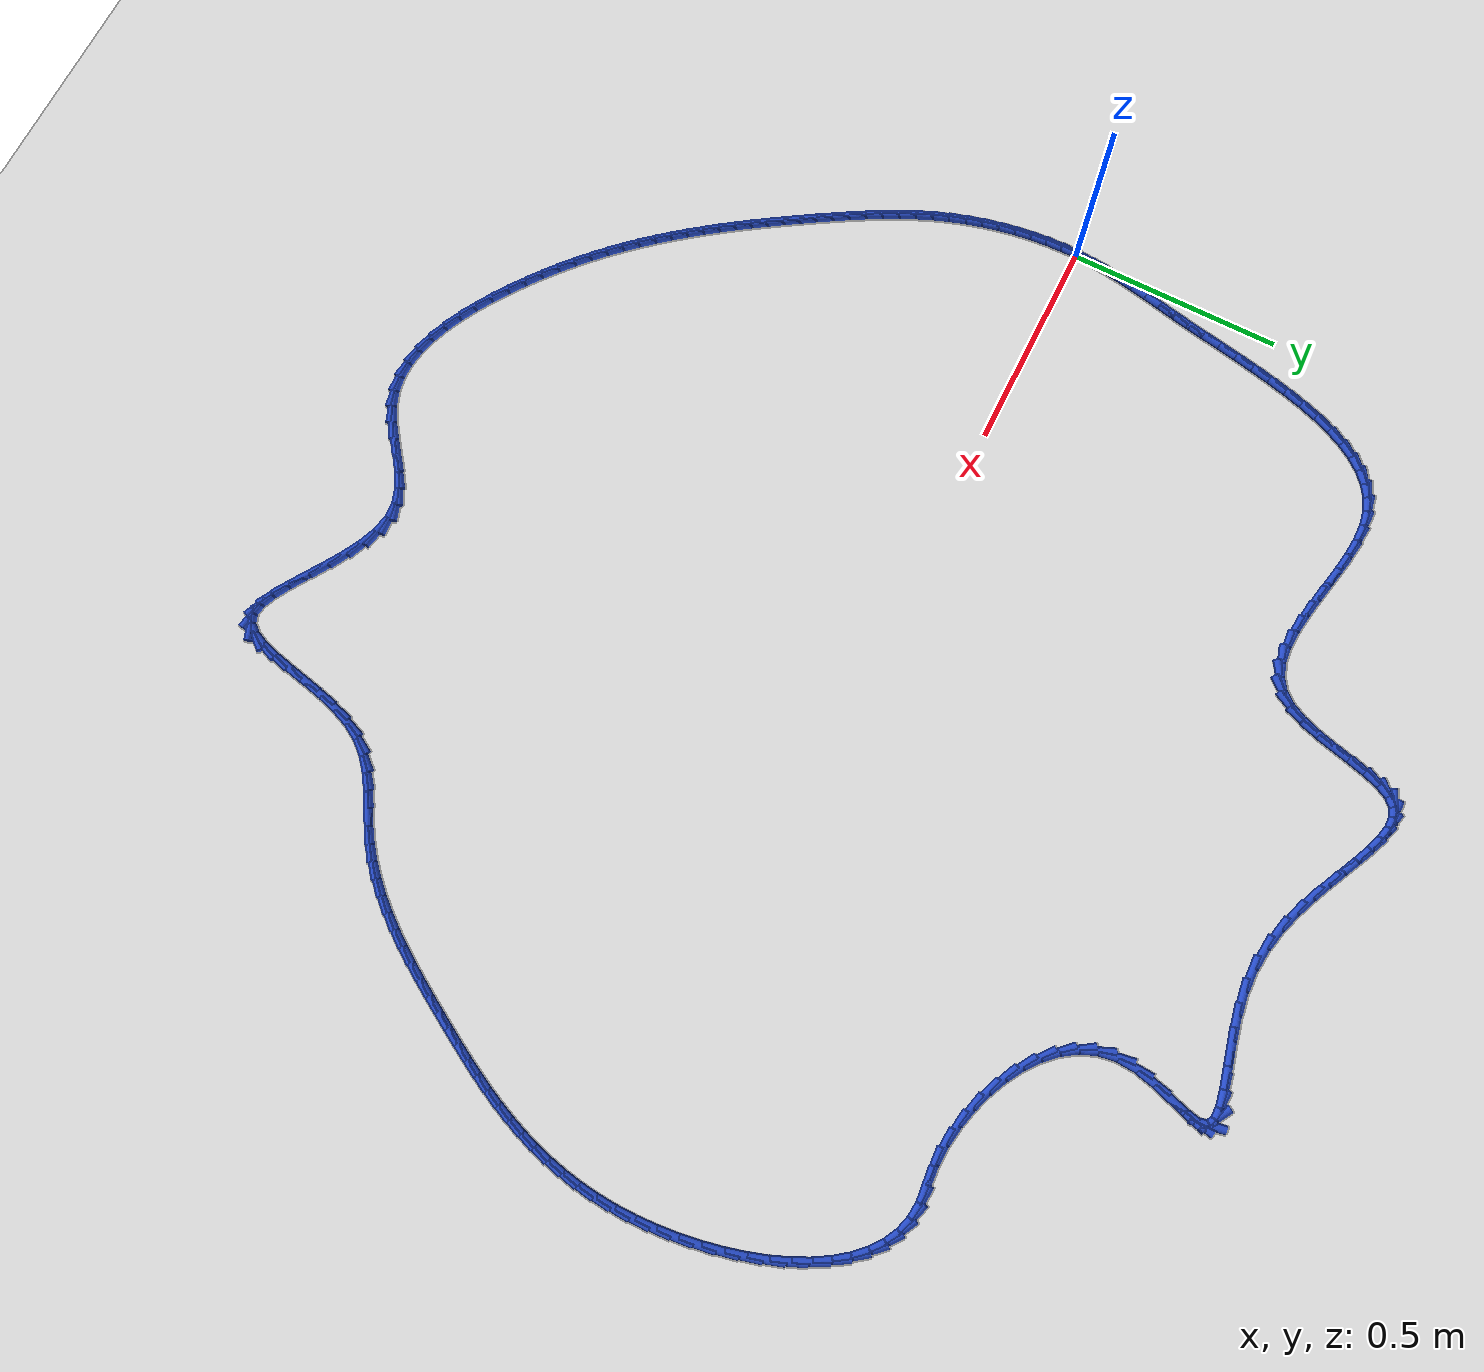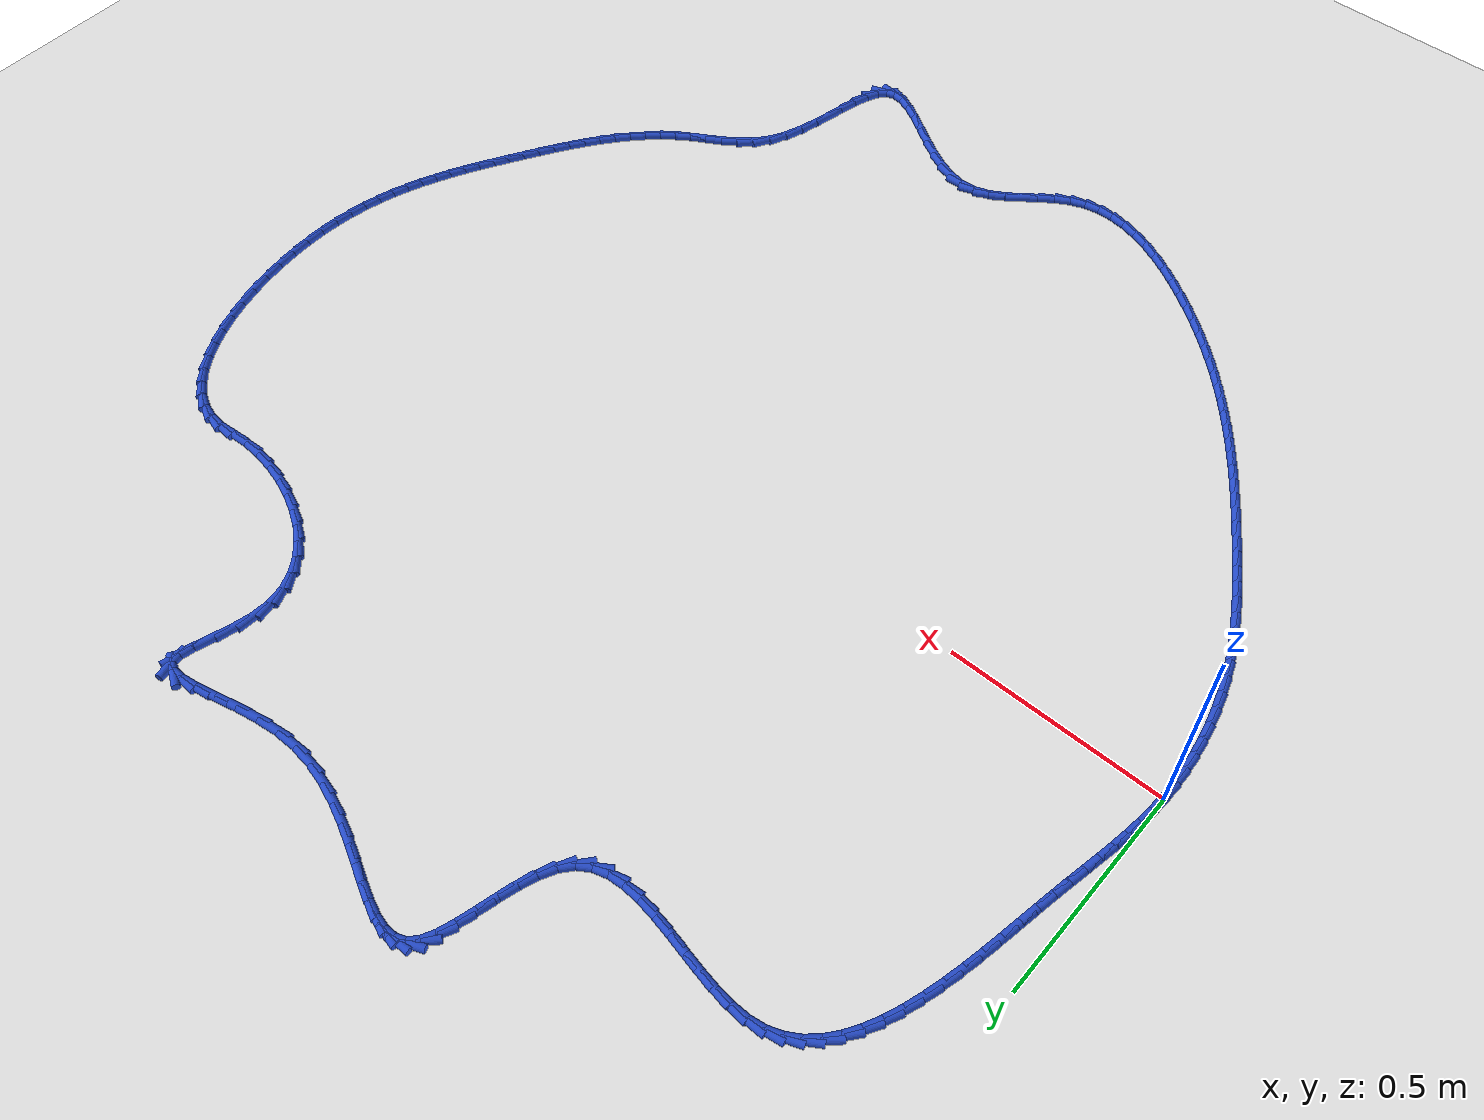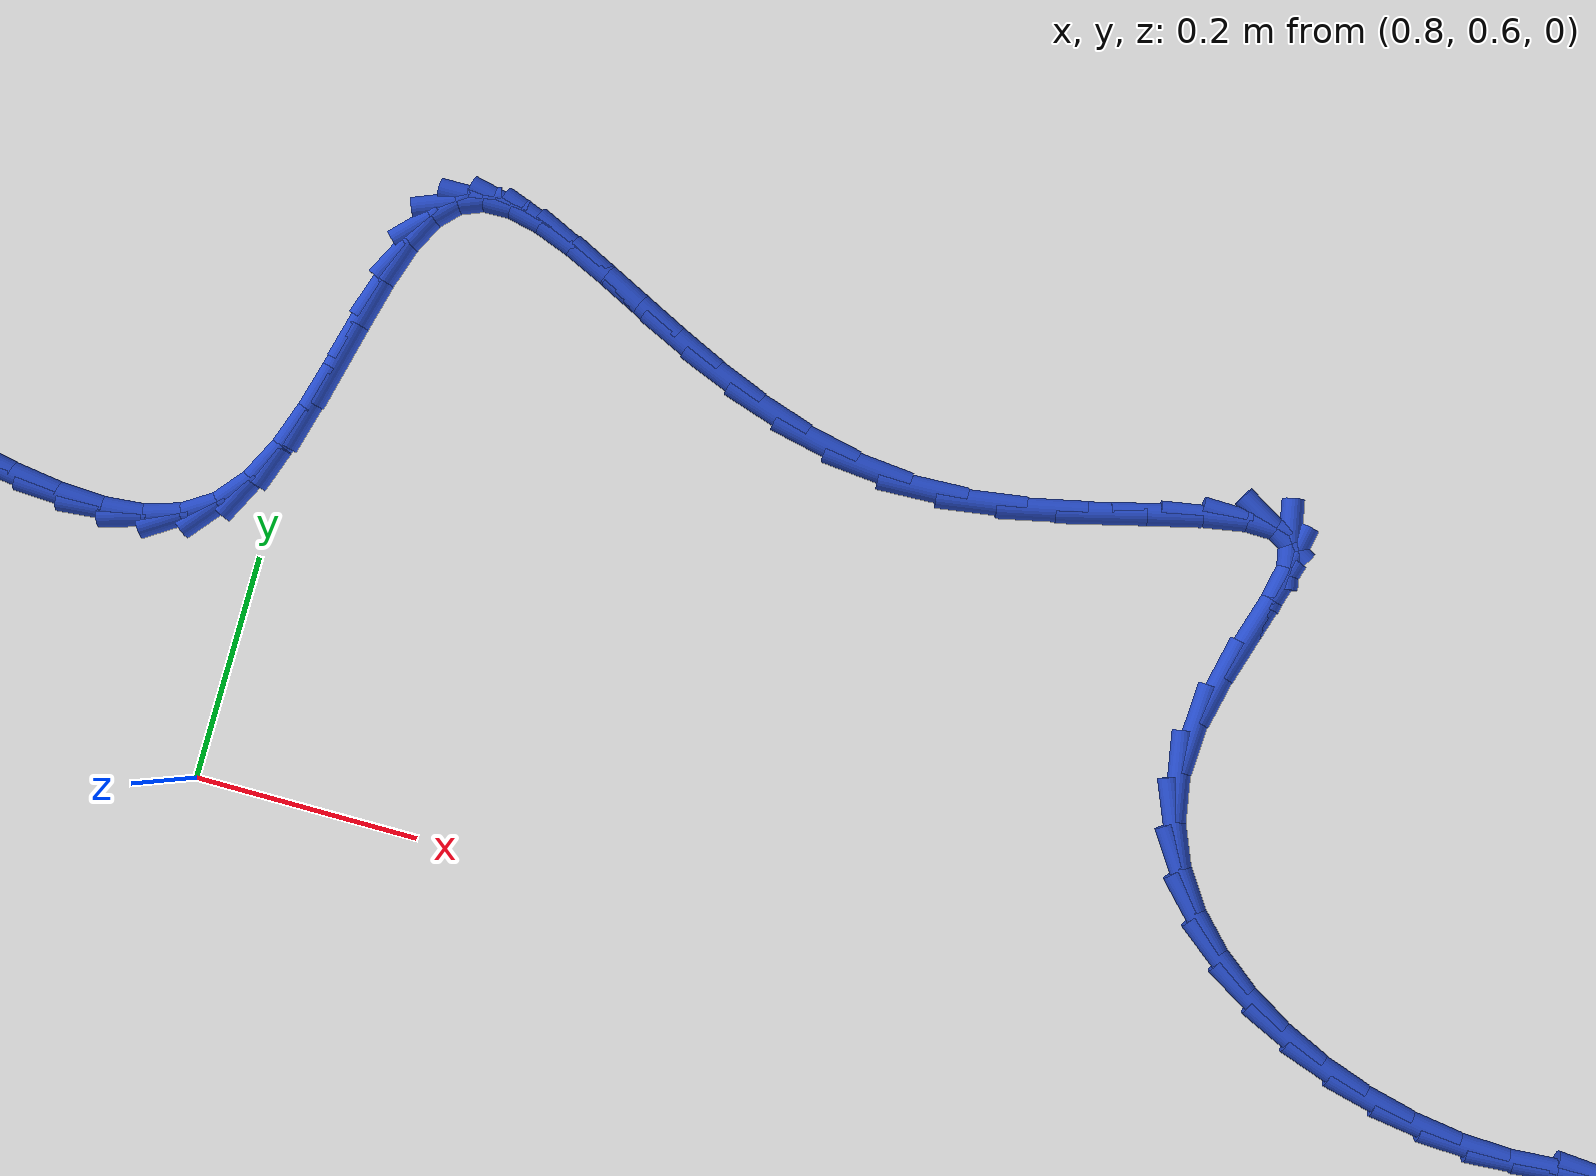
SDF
<sdf version="1.6">
 <world name="default">
  <light name="sun" type="directional">
   <pose>0 0 10 0 -0 0</pose>
   <diffuse>0.8 0.8 0.8 1</diffuse>
   <specular>0.2 0.2 0.2 1</specular>
   <attenuation>
    <range>1000</range>
    <constant>0.9</constant>
    <linear>0.01</linear>
    <quadratic>0.001</quadratic>
   </attenuation>
   <direction>-0.5 0.1 -0.9</direction>
  </light>
  <model name="ground_plane">
   <static>1</static>
   <link name="link">
    <collision name="collision">
     <geometry><plane><normal>0 0 1</normal><size>100 100</size></plane></geometry>
     <surface><friction><ode><mu>100</mu><mu2>50</mu2></ode></friction></surface>
    </collision>
    <visual name="visual">
     <cast_shadows>0</cast_shadows>
     <geometry><plane><normal>0 0 1</normal><size>100 100</size></plane></geometry>
     <material>
      <script><uri>file://media/materials/scripts/gazebo.material</uri><name>Gazebo/WhiteGlow</name></script>
     </material>
    </visual>
   </link>
  </model>
  <gravity>0 0 -9.8</gravity>
  <magnetic_field>6e-06 2.3e-05 -4.2e-05</magnetic_field>
  <atmosphere type="adiabatic"/>
  <physics name="default_physics" default="0" type="ode">
   <max_step_size>0.001</max_step_size>
   <real_time_factor>1</real_time_factor>
   <real_time_update_rate>1000</real_time_update_rate>
  </physics>
  <scene><ambient>0.4 0.4 0.4 1</ambient><background>0.7 0.7 0.7 1</background><shadows>1</shadows></scene>
  <spherical_coordinates>
   <surface_model>EARTH_WGS84</surface_model>
   <latitude_deg>0</latitude_deg>
   <longitude_deg>0</longitude_deg>
   <elevation>0</elevation>
   <heading_deg>0</heading_deg>
  </spherical_coordinates>
  <model name="line">
   <link name="link_0">
    <pose>3.9898639947466563e-17 -6.938893903907228e-18 0.01 0 1.57 1.513052898574908</pose>
    <collision name="collision">
     <geometry><cylinder><radius>0.01</radius><length>0.08</length></cylinder></geometry>
    </collision>
    <visual name="visual">
     <material>
      <script><name>Gazebo/Blue</name><uri>file://media/materials/scripts/gazebo.material</uri></script>
     </material>
     <geometry><cylinder><radius>0.01</radius><length>0.08</length></cylinder></geometry>
    </visual>
   </link>
   <link name="link_1">
    <pose>0.002156272166381357 0.03730078287012222 0.01 0 1.57 1.4685234188009497</pose>
    <collision name="collision">
     <geometry><cylinder><radius>0.01</radius><length>0.08</length></cylinder></geometry>
    </collision>
    <visual name="visual">
     <material>
      <script><name>Gazebo/Blue</name><uri>file://media/materials/scripts/gazebo.material</uri></script>
     </material>
     <geometry><cylinder><radius>0.01</radius><length>0.08</length></cylinder></geometry>
    </visual>
   </link>
   <link name="link_2">
    <pose>0.0059485236757601465 0.07425113811452021 0.01 0 1.57 1.43174111248327</pose>
    <collision name="collision">
     <geometry><cylinder><radius>0.01</radius><length>0.08</length></cylinder></geometry>
    </collision>
    <visual name="visual">
     <material>
      <script><name>Gazebo/Blue</name><uri>file://media/materials/scripts/gazebo.material</uri></script>
     </material>
     <geometry><cylinder><radius>0.01</radius><length>0.08</length></cylinder></geometry>
    </visual>
   </link>
   <link name="link_3">
    <pose>0.01111453466420199 0.11116216472663602 0.01 0 1.57 1.4035440751428823</pose>
    <collision name="collision">
     <geometry><cylinder><radius>0.01</radius><length>0.08</length></cylinder></geometry>
    </collision>
    <visual name="visual">
     <material>
      <script><name>Gazebo/Blue</name><uri>file://media/materials/scripts/gazebo.material</uri></script>
     </material>
     <geometry><cylinder><radius>0.01</radius><length>0.08</length></cylinder></geometry>
    </visual>
   </link>
   <link name="link_4">
    <pose>0.017392085267772462 0.14834496169991185 0.01 0 1.57 1.3842768778832308</pose>
    <collision name="collision">
     <geometry><cylinder><radius>0.01</radius><length>0.08</length></cylinder></geometry>
    </collision>
    <visual name="visual">
     <material>
      <script><name>Gazebo/Blue</name><uri>file://media/materials/scripts/gazebo.material</uri></script>
     </material>
     <geometry><cylinder><radius>0.01</radius><length>0.08</length></cylinder></geometry>
    </visual>
   </link>
   <link name="link_5">
    <pose>0.024518955622537142 0.18611062802778977 0.01 0 1.57 1.3738474238395277</pose>
    <collision name="collision">
     <geometry><cylinder><radius>0.01</radius><length>0.08</length></cylinder></geometry>
    </collision>
    <visual name="visual">
     <material>
      <script><name>Gazebo/Blue</name><uri>file://media/materials/scripts/gazebo.material</uri></script>
     </material>
     <geometry><cylinder><radius>0.01</radius><length>0.08</length></cylinder></geometry>
    </visual>
   </link>
   <link name="link_6">
    <pose>0.032232925864561605 0.22477026270371198 0.01 0 1.57 1.3718115246575833</pose>
    <collision name="collision">
     <geometry><cylinder><radius>0.01</radius><length>0.08</length></cylinder></geometry>
    </collision>
    <visual name="visual">
     <material>
      <script><name>Gazebo/Blue</name><uri>file://media/materials/scripts/gazebo.material</uri></script>
     </material>
     <geometry><cylinder><radius>0.01</radius><length>0.08</length></cylinder></geometry>
    </visual>
   </link>
   <link name="link_7">
    <pose>0.04027177612991146 0.26463496472112075 0.01 0 1.57 1.3774625699937195</pose>
    <collision name="collision">
     <geometry><cylinder><radius>0.01</radius><length>0.08</length></cylinder></geometry>
    </collision>
    <visual name="visual">
     <material>
      <script><name>Gazebo/Blue</name><uri>file://media/materials/scripts/gazebo.material</uri></script>
     </material>
     <geometry><cylinder><radius>0.01</radius><length>0.08</length></cylinder></geometry>
    </visual>
   </link>
   <link name="link_8">
    <pose>0.048373286554652235 0.3060158330734579 0.01 0 1.57 1.387882711639817</pose>
    <collision name="collision">
     <geometry><cylinder><radius>0.01</radius><length>0.08</length></cylinder></geometry>
    </collision>
    <visual name="visual">
     <material>
      <script><name>Gazebo/Blue</name><uri>file://media/materials/scripts/gazebo.material</uri></script>
     </material>
     <geometry><cylinder><radius>0.01</radius><length>0.08</length></cylinder></geometry>
    </visual>
   </link>
   <link name="link_9">
    <pose>0.05634479398032342 0.3491094351761727 0.01 0 1.57 1.3928162767115702</pose>
    <collision name="collision">
     <geometry><cylinder><radius>0.01</radius><length>0.08</length></cylinder></geometry>
    </collision>
    <visual name="visual">
     <material>
      <script><name>Gazebo/Blue</name><uri>file://media/materials/scripts/gazebo.material</uri></script>
     </material>
     <geometry><cylinder><radius>0.01</radius><length>0.08</length></cylinder></geometry>
    </visual>
   </link>
   <link name="link_10">
    <pose>0.06433805610442077 0.3935452175056501 0.01 0 1.57 1.3898911617452134</pose>
    <collision name="collision">
     <geometry><cylinder><radius>0.01</radius><length>0.08</length></cylinder></geometry>
    </collision>
    <visual name="visual">
     <material>
      <script><name>Gazebo/Blue</name><uri>file://media/materials/scripts/gazebo.material</uri></script>
     </material>
     <geometry><cylinder><radius>0.01</radius><length>0.08</length></cylinder></geometry>
    </visual>
   </link>
   <link name="link_11">
    <pose>0.07261124218220193 0.4387774100218494 0.01 0 1.57 1.3794382811619659</pose>
    <collision name="collision">
     <geometry><cylinder><radius>0.01</radius><length>0.08</length></cylinder></geometry>
    </collision>
    <visual name="visual">
     <material>
      <script><name>Gazebo/Blue</name><uri>file://media/materials/scripts/gazebo.material</uri></script>
     </material>
     <geometry><cylinder><radius>0.01</radius><length>0.08</length></cylinder></geometry>
    </visual>
   </link>
   <link name="link_12">
    <pose>0.08142255242970381 0.4842601917049304 0.01 0 1.57 1.3612991322981687</pose>
    <collision name="collision">
     <geometry><cylinder><radius>0.01</radius><length>0.08</length></cylinder></geometry>
    </collision>
    <visual name="visual">
     <material>
      <script><name>Gazebo/Blue</name><uri>file://media/materials/scripts/gazebo.material</uri></script>
     </material>
     <geometry><cylinder><radius>0.01</radius><length>0.08</length></cylinder></geometry>
    </visual>
   </link>
   <link name="link_13">
    <pose>0.09103018706296327 0.529447741535053 0.01 0 1.57 1.3348462763355675</pose>
    <collision name="collision">
     <geometry><cylinder><radius>0.01</radius><length>0.08</length></cylinder></geometry>
    </collision>
    <visual name="visual">
     <material>
      <script><name>Gazebo/Blue</name><uri>file://media/materials/scripts/gazebo.material</uri></script>
     </material>
     <geometry><cylinder><radius>0.01</radius><length>0.08</length></cylinder></geometry>
    </visual>
   </link>
   <link name="link_14">
    <pose>0.1016923462980172 0.5737942384923768 0.01 0 1.57 1.298949519000918</pose>
    <collision name="collision">
     <geometry><cylinder><radius>0.01</radius><length>0.08</length></cylinder></geometry>
    </collision>
    <visual name="visual">
     <material>
      <script><name>Gazebo/Blue</name><uri>file://media/materials/scripts/gazebo.material</uri></script>
     </material>
     <geometry><cylinder><radius>0.01</radius><length>0.08</length></cylinder></geometry>
    </visual>
   </link>
   <link name="link_15">
    <pose>0.11366723035090241 0.6167538615570614 0.01 0 1.57 1.2518966071197488</pose>
    <collision name="collision">
     <geometry><cylinder><radius>0.01</radius><length>0.08</length></cylinder></geometry>
    </collision>
    <visual name="visual">
     <material>
      <script><name>Gazebo/Blue</name><uri>file://media/materials/scripts/gazebo.material</uri></script>
     </material>
     <geometry><cylinder><radius>0.01</radius><length>0.08</length></cylinder></geometry>
    </visual>
   </link>
   <link name="link_16">
    <pose>0.12721303943765588 0.6577807897092668 0.01 0 1.57 1.1912839573119753</pose>
    <collision name="collision">
     <geometry><cylinder><radius>0.01</radius><length>0.08</length></cylinder></geometry>
    </collision>
    <visual name="visual">
     <material>
      <script><name>Gazebo/Blue</name><uri>file://media/materials/scripts/gazebo.material</uri></script>
     </material>
     <geometry><cylinder><radius>0.01</radius><length>0.08</length></cylinder></geometry>
    </visual>
   </link>
   <link name="link_17">
    <pose>0.1425879737743144 0.6963292019291527 0.01 0 1.57 1.1139224576320705</pose>
    <collision name="collision">
     <geometry><cylinder><radius>0.01</radius><length>0.08</length></cylinder></geometry>
    </collision>
    <visual name="visual">
     <material>
      <script><name>Gazebo/Blue</name><uri>file://media/materials/scripts/gazebo.material</uri></script>
     </material>
     <geometry><cylinder><radius>0.01</radius><length>0.08</length></cylinder></geometry>
    </visual>
   </link>
   <link name="link_18">
    <pose>0.16005023357691486 0.7318532771968789 0.01 0 1.57 1.01588296093077</pose>
    <collision name="collision">
     <geometry><cylinder><radius>0.01</radius><length>0.08</length></cylinder></geometry>
    </collision>
    <visual name="visual">
     <material>
      <script><name>Gazebo/Blue</name><uri>file://media/materials/scripts/gazebo.material</uri></script>
     </material>
     <geometry><cylinder><radius>0.01</radius><length>0.08</length></cylinder></geometry>
    </visual>
   </link>
   <link name="link_19">
    <pose>0.17985801906149418 0.7638071944926049 0.01 0 1.57 0.8929710697329993</pose>
    <collision name="collision">
     <geometry><cylinder><radius>0.01</radius><length>0.08</length></cylinder></geometry>
    </collision>
    <visual name="visual">
     <material>
      <script><name>Gazebo/Blue</name><uri>file://media/materials/scripts/gazebo.material</uri></script>
     </material>
     <geometry><cylinder><radius>0.01</radius><length>0.08</length></cylinder></geometry>
    </visual>
   </link>
   <link name="link_20">
    <pose>0.20226953044408924 0.7916451327964911 0.01 0 1.57 0.7421368837041712</pose>
    <collision name="collision">
     <geometry><cylinder><radius>0.01</radius><length>0.08</length></cylinder></geometry>
    </collision>
    <visual name="visual">
     <material>
      <script><name>Gazebo/Blue</name><uri>file://media/materials/scripts/gazebo.material</uri></script>
     </material>
     <geometry><cylinder><radius>0.01</radius><length>0.08</length></cylinder></geometry>
    </visual>
   </link>
   <link name="link_21">
    <pose>0.22754296794073683 0.8148212710886966 0.01 0 1.57 0.5642155621424705</pose>
    <collision name="collision">
     <geometry><cylinder><radius>0.01</radius><length>0.08</length></cylinder></geometry>
    </collision>
    <visual name="visual">
     <material>
      <script><name>Gazebo/Blue</name><uri>file://media/materials/scripts/gazebo.material</uri></script>
     </material>
     <geometry><cylinder><radius>0.01</radius><length>0.08</length></cylinder></geometry>
    </visual>
   </link>
   <link name="link_22">
    <pose>0.2559365317674739 0.8327897883493813 0.01 0 1.57 0.36703995318017646</pose>
    <collision name="collision">
     <geometry><cylinder><radius>0.01</radius><length>0.08</length></cylinder></geometry>
    </collision>
    <visual name="visual">
     <material>
      <script><name>Gazebo/Blue</name><uri>file://media/materials/scripts/gazebo.material</uri></script>
     </material>
     <geometry><cylinder><radius>0.01</radius><length>0.08</length></cylinder></geometry>
    </visual>
   </link>
   <link name="link_23">
    <pose>0.28770842214033737 0.8450048635587052 0.01 0 1.57 0.16705214579408678</pose>
    <collision name="collision">
     <geometry><cylinder><radius>0.01</radius><length>0.08</length></cylinder></geometry>
    </collision>
    <visual name="visual">
     <material>
      <script><name>Gazebo/Blue</name><uri>file://media/materials/scripts/gazebo.material</uri></script>
     </material>
     <geometry><cylinder><radius>0.01</radius><length>0.08</length></cylinder></geometry>
    </visual>
   </link>
   <link name="link_24">
    <pose>0.323089101907152 0.8509708822966459 0.01 0 1.57 0.0048951480218474295</pose>
    <collision name="collision">
     <geometry><cylinder><radius>0.01</radius><length>0.08</length></cylinder></geometry>
    </collision>
    <visual name="visual">
     <material>
      <script><name>Gazebo/Blue</name><uri>file://media/materials/scripts/gazebo.material</uri></script>
     </material>
     <geometry><cylinder><radius>0.01</radius><length>0.08</length></cylinder></geometry>
    </visual>
   </link>
   <link name="link_25">
    <pose>0.36177423542632364 0.8511602532640685 0.01 0 1.57 -0.1025571734178435</pose>
    <collision name="collision">
     <geometry><cylinder><radius>0.01</radius><length>0.08</length></cylinder></geometry>
    </collision>
    <visual name="visual">
     <material>
      <script><name>Gazebo/Blue</name><uri>file://media/materials/scripts/gazebo.material</uri></script>
     </material>
     <geometry><cylinder><radius>0.01</radius><length>0.08</length></cylinder></geometry>
    </visual>
   </link>
   <link name="link_26">
    <pose>0.40297640505811033 0.8469197977728355 0.01 0 1.57 -0.16831279573436056</pose>
    <collision name="collision">
     <geometry><cylinder><radius>0.01</radius><length>0.08</length></cylinder></geometry>
    </collision>
    <visual name="visual">
     <material>
      <script><name>Gazebo/Blue</name><uri>file://media/materials/scripts/gazebo.material</uri></script>
     </material>
     <geometry><cylinder><radius>0.01</radius><length>0.08</length></cylinder></geometry>
    </visual>
   </link>
   <link name="link_27">
    <pose>0.44589083264267937 0.839627760905016 0.01 0 1.57 -0.2018017960738071</pose>
    <collision name="collision">
     <geometry><cylinder><radius>0.01</radius><length>0.08</length></cylinder></geometry>
    </collision>
    <visual name="visual">
     <material>
      <script><name>Gazebo/Blue</name><uri>file://media/materials/scripts/gazebo.material</uri></script>
     </material>
     <geometry><cylinder><radius>0.01</radius><length>0.08</length></cylinder></geometry>
    </visual>
   </link>
   <link name="link_28">
    <pose>0.4897127400201986 0.8306623877426786 0.01 0 1.57 -0.20778349624121784</pose>
    <collision name="collision">
     <geometry><cylinder><radius>0.01</radius><length>0.08</length></cylinder></geometry>
    </collision>
    <visual name="visual">
     <material>
      <script><name>Gazebo/Blue</name><uri>file://media/materials/scripts/gazebo.material</uri></script>
     </material>
     <geometry><cylinder><radius>0.01</radius><length>0.08</length></cylinder></geometry>
    </visual>
   </link>
   <link name="link_29">
    <pose>0.5336373490308353 0.8214019233678924 0.01 0 1.57 -0.1869809368948122</pose>
    <collision name="collision">
     <geometry><cylinder><radius>0.01</radius><length>0.08</length></cylinder></geometry>
    </collision>
    <visual name="visual">
     <material>
      <script><name>Gazebo/Blue</name><uri>file://media/materials/scripts/gazebo.material</uri></script>
     </material>
     <geometry><cylinder><radius>0.01</radius><length>0.08</length></cylinder></geometry>
    </visual>
   </link>
   <link name="link_30">
    <pose>0.5768598815147576 0.8132246128627261 0.01 0 1.57 -0.13617272997016291</pose>
    <collision name="collision">
     <geometry><cylinder><radius>0.01</radius><length>0.08</length></cylinder></geometry>
    </collision>
    <visual name="visual">
     <material>
      <script><name>Gazebo/Blue</name><uri>file://media/materials/scripts/gazebo.material</uri></script>
     </material>
     <geometry><cylinder><radius>0.01</radius><length>0.08</length></cylinder></geometry>
    </visual>
   </link>
   <link name="link_31">
    <pose>0.6185755593121329 0.8075087013092489 0.01 0 1.57 -0.04758017688392564</pose>
    <collision name="collision">
     <geometry><cylinder><radius>0.01</radius><length>0.08</length></cylinder></geometry>
    </collision>
    <visual name="visual">
     <material>
      <script><name>Gazebo/Blue</name><uri>file://media/materials/scripts/gazebo.material</uri></script>
     </material>
     <geometry><cylinder><radius>0.01</radius><length>0.08</length></cylinder></geometry>
    </visual>
   </link>
   <link name="link_32">
    <pose>0.657979604263129 0.8056324337895296 0.01 0 1.57 0.09182807816345351</pose>
    <collision name="collision">
     <geometry><cylinder><radius>0.01</radius><length>0.08</length></cylinder></geometry>
    </collision>
    <visual name="visual">
     <material>
      <script><name>Gazebo/Blue</name><uri>file://media/materials/scripts/gazebo.material</uri></script>
     </material>
     <geometry><cylinder><radius>0.01</radius><length>0.08</length></cylinder></geometry>
    </visual>
   </link>
   <link name="link_33">
    <pose>0.6942672382079128 0.8089740553856369 0.01 0 1.57 0.29790187421238473</pose>
    <collision name="collision">
     <geometry><cylinder><radius>0.01</radius><length>0.08</length></cylinder></geometry>
    </collision>
    <visual name="visual">
     <material>
      <script><name>Gazebo/Blue</name><uri>file://media/materials/scripts/gazebo.material</uri></script>
     </material>
     <geometry><cylinder><radius>0.01</radius><length>0.08</length></cylinder></geometry>
    </visual>
   </link>
   <link name="link_34">
    <pose>0.7266336829866523 0.8189118111796401 0.01 0 1.57 0.5749961321220008</pose>
    <collision name="collision">
     <geometry><cylinder><radius>0.01</radius><length>0.08</length></cylinder></geometry>
    </collision>
    <visual name="visual">
     <material>
      <script><name>Gazebo/Blue</name><uri>file://media/materials/scripts/gazebo.material</uri></script>
     </material>
     <geometry><cylinder><radius>0.01</radius><length>0.08</length></cylinder></geometry>
    </visual>
   </link>
   <link name="link_35">
    <pose>0.7542741604395155 0.8368239462536078 0.01 0 1.57 0.8809593541204325</pose>
    <collision name="collision">
     <geometry><cylinder><radius>0.01</radius><length>0.08</length></cylinder></geometry>
    </collision>
    <visual name="visual">
     <material>
      <script><name>Gazebo/Blue</name><uri>file://media/materials/scripts/gazebo.material</uri></script>
     </material>
     <geometry><cylinder><radius>0.01</radius><length>0.08</length></cylinder></geometry>
    </visual>
   </link>
   <link name="link_36">
    <pose>0.776532320667093 0.8638015049139302 0.01 0 1.57 1.1048324555072642</pose>
    <collision name="collision">
     <geometry><cylinder><radius>0.01</radius><length>0.08</length></cylinder></geometry>
    </collision>
    <visual name="visual">
     <material>
      <script><name>Gazebo/Blue</name><uri>file://media/materials/scripts/gazebo.material</uri></script>
     </material>
     <geometry><cylinder><radius>0.01</radius><length>0.08</length></cylinder></geometry>
    </visual>
   </link>
   <link name="link_37">
    <pose>0.7939961411705915 0.8985278242444248 0.01 0 1.57 1.2364931587931693</pose>
    <collision name="collision">
     <geometry><cylinder><radius>0.01</radius><length>0.08</length></cylinder></geometry>
    </collision>
    <visual name="visual">
     <material>
      <script><name>Gazebo/Blue</name><uri>file://media/materials/scripts/gazebo.material</uri></script>
     </material>
     <geometry><cylinder><radius>0.01</radius><length>0.08</length></cylinder></geometry>
    </visual>
   </link>
   <link name="link_38">
    <pose>0.8078746848971028 0.9384844740824818 0.01 0 1.57 1.3073294869404763</pose>
    <collision name="collision">
     <geometry><cylinder><radius>0.01</radius><length>0.08</length></cylinder></geometry>
    </collision>
    <visual name="visual">
     <material>
      <script><name>Gazebo/Blue</name><uri>file://media/materials/scripts/gazebo.material</uri></script>
     </material>
     <geometry><cylinder><radius>0.01</radius><length>0.08</length></cylinder></geometry>
    </visual>
   </link>
   <link name="link_39">
    <pose>0.8193815904170296 0.981144170678174 0.01 0 1.57 1.3337421506004719</pose>
    <collision name="collision">
     <geometry><cylinder><radius>0.01</radius><length>0.08</length></cylinder></geometry>
    </collision>
    <visual name="visual">
     <material>
      <script><name>Gazebo/Blue</name><uri>file://media/materials/scripts/gazebo.material</uri></script>
     </material>
     <geometry><cylinder><radius>0.01</radius><length>0.08</length></cylinder></geometry>
    </visual>
   </link>
   <link name="link_40">
    <pose>0.8297304963007744 1.0239796302815742 0.01 0 1.57 1.3192363589302447</pose>
    <collision name="collision">
     <geometry><cylinder><radius>0.01</radius><length>0.08</length></cylinder></geometry>
    </collision>
    <visual name="visual">
     <material>
      <script><name>Gazebo/Blue</name><uri>file://media/materials/scripts/gazebo.material</uri></script>
     </material>
     <geometry><cylinder><radius>0.01</radius><length>0.08</length></cylinder></geometry>
    </visual>
   </link>
   <link name="link_41">
    <pose>0.8401350411187394 1.0644635691427549 0.01 0 1.57 1.2539716437456518</pose>
    <collision name="collision">
     <geometry><cylinder><radius>0.01</radius><length>0.08</length></cylinder></geometry>
    </collision>
    <visual name="visual">
     <material>
      <script><name>Gazebo/Blue</name><uri>file://media/materials/scripts/gazebo.material</uri></script>
     </material>
     <geometry><cylinder><radius>0.01</radius><length>0.08</length></cylinder></geometry>
    </visual>
   </link>
   <link name="link_42">
    <pose>0.8518088634413274 1.1000687035117886 0.01 0 1.57 1.1055268505615456</pose>
    <collision name="collision">
     <geometry><cylinder><radius>0.01</radius><length>0.08</length></cylinder></geometry>
    </collision>
    <visual name="visual">
     <material>
      <script><name>Gazebo/Blue</name><uri>file://media/materials/scripts/gazebo.material</uri></script>
     </material>
     <geometry><cylinder><radius>0.01</radius><length>0.08</length></cylinder></geometry>
    </visual>
   </link>
   <link name="link_43">
    <pose>0.8659656018389409 1.1282677496387492 0.01 0 1.57 0.8045636507098258</pose>
    <collision name="collision">
     <geometry><cylinder><radius>0.01</radius><length>0.08</length></cylinder></geometry>
    </collision>
    <visual name="visual">
     <material>
      <script><name>Gazebo/Blue</name><uri>file://media/materials/scripts/gazebo.material</uri></script>
     </material>
     <geometry><cylinder><radius>0.01</radius><length>0.08</length></cylinder></geometry>
    </visual>
   </link>
   <link name="link_44">
    <pose>0.8837441192683011 1.1467411375816514 0.01 0 1.57 0.38201412358622233</pose>
    <collision name="collision">
     <geometry><cylinder><radius>0.01</radius><length>0.08</length></cylinder></geometry>
    </collision>
    <visual name="visual">
     <material>
      <script><name>Gazebo/Blue</name><uri>file://media/materials/scripts/gazebo.material</uri></script>
     </material>
     <geometry><cylinder><radius>0.01</radius><length>0.08</length></cylinder></geometry>
    </visual>
   </link>
   <link name="link_45">
    <pose>0.9054570846926641 1.155464322367687 0.01 0 1.57 0.014703957135934961</pose>
    <collision name="collision">
     <geometry><cylinder><radius>0.01</radius><length>0.08</length></cylinder></geometry>
    </collision>
    <visual name="visual">
     <material>
      <script><name>Gazebo/Blue</name><uri>file://media/materials/scripts/gazebo.material</uri></script>
     </material>
     <geometry><cylinder><radius>0.01</radius><length>0.08</length></cylinder></geometry>
    </visual>
   </link>
   <link name="link_46">
    <pose>0.9309039030651887 1.1558385182625148 0.01 0 1.57 -0.22241087092429207</pose>
    <collision name="collision">
     <geometry><cylinder><radius>0.01</radius><length>0.08</length></cylinder></geometry>
    </collision>
    <visual name="visual">
     <material>
      <script><name>Gazebo/Blue</name><uri>file://media/materials/scripts/gazebo.material</uri></script>
     </material>
     <geometry><cylinder><radius>0.01</radius><length>0.08</length></cylinder></geometry>
    </visual>
   </link>
   <link name="link_47">
    <pose>0.9598762706227636 1.1492863530211925 0.01 0 1.57 -0.3573388477864341</pose>
    <collision name="collision">
     <geometry><cylinder><radius>0.01</radius><length>0.08</length></cylinder></geometry>
    </collision>
    <visual name="visual">
     <material>
      <script><name>Gazebo/Blue</name><uri>file://media/materials/scripts/gazebo.material</uri></script>
     </material>
     <geometry><cylinder><radius>0.01</radius><length>0.08</length></cylinder></geometry>
    </visual>
   </link>
   <link name="link_48">
    <pose>0.992165883602278 1.1372304543987786 0.01 0 1.57 -0.4277215308155489</pose>
    <collision name="collision">
     <geometry><cylinder><radius>0.01</radius><length>0.08</length></cylinder></geometry>
    </collision>
    <visual name="visual">
     <material>
      <script><name>Gazebo/Blue</name><uri>file://media/materials/scripts/gazebo.material</uri></script>
     </material>
     <geometry><cylinder><radius>0.01</radius><length>0.08</length></cylinder></geometry>
    </visual>
   </link>
   <link name="link_49">
    <pose>1.02756443824062 1.1210934501503305 0.01 0 1.57 -0.456223491454132</pose>
    <collision name="collision">
     <geometry><cylinder><radius>0.01</radius><length>0.08</length></cylinder></geometry>
    </collision>
    <visual name="visual">
     <material>
      <script><name>Gazebo/Blue</name><uri>file://media/materials/scripts/gazebo.material</uri></script>
     </material>
     <geometry><cylinder><radius>0.01</radius><length>0.08</length></cylinder></geometry>
    </visual>
   </link>
   <link name="link_50">
    <pose>1.0658636307746783 1.102297968030906 0.01 0 1.57 -0.45454265264558885</pose>
    <collision name="collision">
     <geometry><cylinder><radius>0.01</radius><length>0.08</length></cylinder></geometry>
    </collision>
    <visual name="visual">
     <material>
      <script><name>Gazebo/Blue</name><uri>file://media/materials/scripts/gazebo.material</uri></script>
     </material>
     <geometry><cylinder><radius>0.01</radius><length>0.08</length></cylinder></geometry>
    </visual>
   </link>
   <link name="link_51">
    <pose>1.106855157441342 1.0822666357955635 0.01 0 1.57 -0.4282073848165518</pose>
    <collision name="collision">
     <geometry><cylinder><radius>0.01</radius><length>0.08</length></cylinder></geometry>
    </collision>
    <visual name="visual">
     <material>
      <script><name>Gazebo/Blue</name><uri>file://media/materials/scripts/gazebo.material</uri></script>
     </material>
     <geometry><cylinder><radius>0.01</radius><length>0.08</length></cylinder></geometry>
    </visual>
   </link>
   <link name="link_52">
    <pose>1.1503307144775 1.0624220811993605 0.01 0 1.57 -0.37927414412389016</pose>
    <collision name="collision">
     <geometry><cylinder><radius>0.01</radius><length>0.08</length></cylinder></geometry>
    </collision>
    <visual name="visual">
     <material>
      <script><name>Gazebo/Blue</name><uri>file://media/materials/scripts/gazebo.material</uri></script>
     </material>
     <geometry><cylinder><radius>0.01</radius><length>0.08</length></cylinder></geometry>
    </visual>
   </link>
   <link name="link_53">
    <pose>1.1960819981200403 1.0441869319973553 0.01 0 1.57 -0.30782627491140113</pose>
    <collision name="collision">
     <geometry><cylinder><radius>0.01</radius><length>0.08</length></cylinder></geometry>
    </collision>
    <visual name="visual">
     <material>
      <script><name>Gazebo/Blue</name><uri>file://media/materials/scripts/gazebo.material</uri></script>
     </material>
     <geometry><cylinder><radius>0.01</radius><length>0.08</length></cylinder></geometry>
    </visual>
   </link>
   <link name="link_54">
    <pose>1.243900704605852 1.0289838159446056 0.01 0 1.57 -0.21307879995680593</pose>
    <collision name="collision">
     <geometry><cylinder><radius>0.01</radius><length>0.08</length></cylinder></geometry>
    </collision>
    <visual name="visual">
     <material>
      <script><name>Gazebo/Blue</name><uri>file://media/materials/scripts/gazebo.material</uri></script>
     </material>
     <geometry><cylinder><radius>0.01</radius><length>0.08</length></cylinder></geometry>
    </visual>
   </link>
   <link name="link_55">
    <pose>1.2935785301718234 1.0182353607961694 0.01 0 1.57 -0.09461815459993521</pose>
    <collision name="collision">
     <geometry><cylinder><radius>0.01</radius><length>0.08</length></cylinder></geometry>
    </collision>
    <visual name="visual">
     <material>
      <script><name>Gazebo/Blue</name><uri>file://media/materials/scripts/gazebo.material</uri></script>
     </material>
     <geometry><cylinder><radius>0.01</radius><length>0.08</length></cylinder></geometry>
    </visual>
   </link>
   <link name="link_56">
    <pose>1.3449071710548441 1.0133641943071048 0.01 0 1.57 0.03990790814757379</pose>
    <collision name="collision">
     <geometry><cylinder><radius>0.01</radius><length>0.08</length></cylinder></geometry>
    </collision>
    <visual name="visual">
     <material>
      <script><name>Gazebo/Blue</name><uri>file://media/materials/scripts/gazebo.material</uri></script>
     </material>
     <geometry><cylinder><radius>0.01</radius><length>0.08</length></cylinder></geometry>
    </visual>
   </link>
   <link name="link_57">
    <pose>1.397547340767767 1.0154660693275792 0.01 0 1.57 0.14602108599088523</pose>
    <collision name="collision">
     <geometry><cylinder><radius>0.01</radius><length>0.08</length></cylinder></geometry>
    </collision>
    <visual name="visual">
     <material>
      <script><name>Gazebo/Blue</name><uri>file://media/materials/scripts/gazebo.material</uri></script>
     </material>
     <geometry><cylinder><radius>0.01</radius><length>0.08</length></cylinder></geometry>
    </visual>
   </link>
   <link name="link_58">
    <pose>1.4501863579885346 1.0232075760343877 0.01 0 1.57 0.21202147658183204</pose>
    <collision name="collision">
     <geometry><cylinder><radius>0.01</radius><length>0.08</length></cylinder></geometry>
    </collision>
    <visual name="visual">
     <material>
      <script><name>Gazebo/Blue</name><uri>file://media/materials/scripts/gazebo.material</uri></script>
     </material>
     <geometry><cylinder><radius>0.01</radius><length>0.08</length></cylinder></geometry>
    </visual>
   </link>
   <link name="link_59">
    <pose>1.5010731603951404 1.03416129966039 0.01 0 1.57 0.24275066964086753</pose>
    <collision name="collision">
     <geometry><cylinder><radius>0.01</radius><length>0.08</length></cylinder></geometry>
    </collision>
    <visual name="visual">
     <material>
      <script><name>Gazebo/Blue</name><uri>file://media/materials/scripts/gazebo.material</uri></script>
     </material>
     <geometry><cylinder><radius>0.01</radius><length>0.08</length></cylinder></geometry>
    </visual>
   </link>
   <link name="link_60">
    <pose>1.5484545723704946 1.045894551589285 0.01 0 1.57 0.23488512355423014</pose>
    <collision name="collision">
     <geometry><cylinder><radius>0.01</radius><length>0.08</length></cylinder></geometry>
    </collision>
    <visual name="visual">
     <material>
      <script><name>Gazebo/Blue</name><uri>file://media/materials/scripts/gazebo.material</uri></script>
     </material>
     <geometry><cylinder><radius>0.01</radius><length>0.08</length></cylinder></geometry>
    </visual>
   </link>
   <link name="link_61">
    <pose>1.5905774182975063 1.0559746432047719 0.01 0 1.57 0.1690919249045621</pose>
    <collision name="collision">
     <geometry><cylinder><radius>0.01</radius><length>0.08</length></cylinder></geometry>
    </collision>
    <visual name="visual">
     <material>
      <script><name>Gazebo/Blue</name><uri>file://media/materials/scripts/gazebo.material</uri></script>
     </material>
     <geometry><cylinder><radius>0.01</radius><length>0.08</length></cylinder></geometry>
    </visual>
   </link>
   <link name="link_62">
    <pose>1.6256885225590854 1.0619688858905487 0.01 0 1.57 -0.019897591515101582</pose>
    <collision name="collision">
     <geometry><cylinder><radius>0.01</radius><length>0.08</length></cylinder></geometry>
    </collision>
    <visual name="visual">
     <material>
      <script><name>Gazebo/Blue</name><uri>file://media/materials/scripts/gazebo.material</uri></script>
     </material>
     <geometry><cylinder><radius>0.01</radius><length>0.08</length></cylinder></geometry>
    </visual>
   </link>
   <link name="link_63">
    <pose>1.6520347095381425 1.061444591030315 0.01 0 1.57 -0.5394277736495552</pose>
    <collision name="collision">
     <geometry><cylinder><radius>0.01</radius><length>0.08</length></cylinder></geometry>
    </collision>
    <visual name="visual">
     <material>
      <script><name>Gazebo/Blue</name><uri>file://media/materials/scripts/gazebo.material</uri></script>
     </material>
     <geometry><cylinder><radius>0.01</radius><length>0.08</length></cylinder></geometry>
    </visual>
   </link>
   <link name="link_64">
    <pose>1.6678628036175867 1.0519690700077695 0.01 0 1.57 -1.3884980067033423</pose>
    <collision name="collision">
     <geometry><cylinder><radius>0.01</radius><length>0.08</length></cylinder></geometry>
    </collision>
    <visual name="visual">
     <material>
      <script><name>Gazebo/Blue</name><uri>file://media/materials/scripts/gazebo.material</uri></script>
     </material>
     <geometry><cylinder><radius>0.01</radius><length>0.08</length></cylinder></geometry>
    </visual>
   </link>
   <link name="link_65">
    <pose>1.6716682652834587 1.0313259135309352 0.01 0 1.57 1.3704632028188735</pose>
    <collision name="collision">
     <geometry><cylinder><radius>0.01</radius><length>0.08</length></cylinder></geometry>
    </collision>
    <visual name="visual">
     <material>
      <script><name>Gazebo/Blue</name><uri>file://media/materials/scripts/gazebo.material</uri></script>
     </material>
     <geometry><cylinder><radius>0.01</radius><length>0.08</length></cylinder></geometry>
    </visual>
   </link>
   <link name="link_66">
    <pose>1.6653621019121887 1.0002697698668617 0.01 0 1.57 1.2684679301327535</pose>
    <collision name="collision">
     <geometry><cylinder><radius>0.01</radius><length>0.08</length></cylinder></geometry>
    </collision>
    <visual name="visual">
     <material>
      <script><name>Gazebo/Blue</name><uri>file://media/materials/scripts/gazebo.material</uri></script>
     </material>
     <geometry><cylinder><radius>0.01</radius><length>0.08</length></cylinder></geometry>
    </visual>
   </link>
   <link name="link_67">
    <pose>1.6533369624415235 0.9617139752339451 0.01 0 1.57 1.2715331208141134</pose>
    <collision name="collision">
     <geometry><cylinder><radius>0.01</radius><length>0.08</length></cylinder></geometry>
    </collision>
    <visual name="visual">
     <material>
      <script><name>Gazebo/Blue</name><uri>file://media/materials/scripts/gazebo.material</uri></script>
     </material>
     <geometry><cylinder><radius>0.01</radius><length>0.08</length></cylinder></geometry>
    </visual>
   </link>
   <link name="link_68">
    <pose>1.6400413564662728 0.9186204569643149 0.01 0 1.57 1.3480554073481932</pose>
    <collision name="collision">
     <geometry><cylinder><radius>0.01</radius><length>0.08</length></cylinder></geometry>
    </collision>
    <visual name="visual">
     <material>
      <script><name>Gazebo/Blue</name><uri>file://media/materials/scripts/gazebo.material</uri></script>
     </material>
     <geometry><cylinder><radius>0.01</radius><length>0.08</length></cylinder></geometry>
    </visual>
   </link>
   <link name="link_69">
    <pose>1.6299237935812438 0.8739511423901012 0.01 0 1.57 1.511319059028461</pose>
    <collision name="collision">
     <geometry><cylinder><radius>0.01</radius><length>0.08</length></cylinder></geometry>
    </collision>
    <visual name="visual">
     <material>
      <script><name>Gazebo/Blue</name><uri>file://media/materials/scripts/gazebo.material</uri></script>
     </material>
     <geometry><cylinder><radius>0.01</radius><length>0.08</length></cylinder></geometry>
    </visual>
   </link>
   <link name="link_70">
    <pose>1.6273436820914073 0.8306225153639418 0.01 0 1.57 -1.4035199156314206</pose>
    <collision name="collision">
     <geometry><cylinder><radius>0.01</radius><length>0.08</length></cylinder></geometry>
    </collision>
    <visual name="visual">
     <material>
      <script><name>Gazebo/Blue</name><uri>file://media/materials/scripts/gazebo.material</uri></script>
     </material>
     <geometry><cylinder><radius>0.01</radius><length>0.08</length></cylinder></geometry>
    </visual>
   </link>
   <link name="link_71">
    <pose>1.6341566851001752 0.790274098496667 0.01 0 1.57 -1.18066678724124</pose>
    <collision name="collision">
     <geometry><cylinder><radius>0.01</radius><length>0.08</length></cylinder></geometry>
    </collision>
    <visual name="visual">
     <material>
      <script><name>Gazebo/Blue</name><uri>file://media/materials/scripts/gazebo.material</uri></script>
     </material>
     <geometry><cylinder><radius>0.01</radius><length>0.08</length></cylinder></geometry>
    </visual>
   </link>
   <link name="link_72">
    <pose>1.649432772611692 0.7531246539650479 0.01 0 1.57 -0.9802156688617786</pose>
    <collision name="collision">
     <geometry><cylinder><radius>0.01</radius><length>0.08</length></cylinder></geometry>
    </collision>
    <visual name="visual">
     <material>
      <script><name>Gazebo/Blue</name><uri>file://media/materials/scripts/gazebo.material</uri></script>
     </material>
     <geometry><cylinder><radius>0.01</radius><length>0.08</length></cylinder></geometry>
    </visual>
   </link>
   <link name="link_73">
    <pose>1.6720962223998974 0.7193186379297771 0.01 0 1.57 -0.8080451354325076</pose>
    <collision name="collision">
     <geometry><cylinder><radius>0.01</radius><length>0.08</length></cylinder></geometry>
    </collision>
    <visual name="visual">
     <material>
      <script><name>Gazebo/Blue</name><uri>file://media/materials/scripts/gazebo.material</uri></script>
     </material>
     <geometry><cylinder><radius>0.01</radius><length>0.08</length></cylinder></geometry>
    </visual>
   </link>
   <link name="link_74">
    <pose>1.701071312238731 0.6890005065515475 0.01 0 1.57 -0.6624481850245808</pose>
    <collision name="collision">
     <geometry><cylinder><radius>0.01</radius><length>0.08</length></cylinder></geometry>
    </collision>
    <visual name="visual">
     <material>
      <script><name>Gazebo/Blue</name><uri>file://media/materials/scripts/gazebo.material</uri></script>
     </material>
     <geometry><cylinder><radius>0.01</radius><length>0.08</length></cylinder></geometry>
    </visual>
   </link>
   <link name="link_75">
    <pose>1.735282319902133 0.6623147159910514 0.01 0 1.57 -0.5382373127173165</pose>
    <collision name="collision">
     <geometry><cylinder><radius>0.01</radius><length>0.08</length></cylinder></geometry>
    </collision>
    <visual name="visual">
     <material>
      <script><name>Gazebo/Blue</name><uri>file://media/materials/scripts/gazebo.material</uri></script>
     </material>
     <geometry><cylinder><radius>0.01</radius><length>0.08</length></cylinder></geometry>
    </visual>
   </link>
   <link name="link_76">
    <pose>1.7736535231640427 0.639405722408982 0.01 0 1.57 -0.4295075258254783</pose>
    <collision name="collision">
     <geometry><cylinder><radius>0.01</radius><length>0.08</length></cylinder></geometry>
    </collision>
    <visual name="visual">
     <material>
      <script><name>Gazebo/Blue</name><uri>file://media/materials/scripts/gazebo.material</uri></script>
     </material>
     <geometry><cylinder><radius>0.01</radius><length>0.08</length></cylinder></geometry>
    </visual>
   </link>
   <link name="link_77">
    <pose>1.8151091997984001 0.6204179819660315 0.01 0 1.57 -0.3307078404261728</pose>
    <collision name="collision">
     <geometry><cylinder><radius>0.01</radius><length>0.08</length></cylinder></geometry>
    </collision>
    <visual name="visual">
     <material>
      <script><name>Gazebo/Blue</name><uri>file://media/materials/scripts/gazebo.material</uri></script>
     </material>
     <geometry><cylinder><radius>0.01</radius><length>0.08</length></cylinder></geometry>
    </visual>
   </link>
   <link name="link_78">
    <pose>1.8585736275791451 0.6054959508228928 0.01 0 1.57 -0.23674740963121657</pose>
    <collision name="collision">
     <geometry><cylinder><radius>0.01</radius><length>0.08</length></cylinder></geometry>
    </collision>
    <visual name="visual">
     <material>
      <script><name>Gazebo/Blue</name><uri>file://media/materials/scripts/gazebo.material</uri></script>
     </material>
     <geometry><cylinder><radius>0.01</radius><length>0.08</length></cylinder></geometry>
    </visual>
   </link>
   <link name="link_79">
    <pose>1.902971084280217 0.5947840851402583 0.01 0 1.57 -0.1426750154057019</pose>
    <collision name="collision">
     <geometry><cylinder><radius>0.01</radius><length>0.08</length></cylinder></geometry>
    </collision>
    <visual name="visual">
     <material>
      <script><name>Gazebo/Blue</name><uri>file://media/materials/scripts/gazebo.material</uri></script>
     </material>
     <geometry><cylinder><radius>0.01</radius><length>0.08</length></cylinder></geometry>
    </visual>
   </link>
   <link name="link_80">
    <pose>1.947225847675556 0.5884268410788208 0.01 0 1.57 -0.04314987171424927</pose>
    <collision name="collision">
     <geometry><cylinder><radius>0.01</radius><length>0.08</length></cylinder></geometry>
    </collision>
    <visual name="visual">
     <material>
      <script><name>Gazebo/Blue</name><uri>file://media/materials/scripts/gazebo.material</uri></script>
     </material>
     <geometry><cylinder><radius>0.01</radius><length>0.08</length></cylinder></geometry>
    </visual>
   </link>
   <link name="link_81">
    <pose>1.9902621955391018 0.5865686747992731 0.01 0 1.57 0.067084478952186</pose>
    <collision name="collision">
     <geometry><cylinder><radius>0.01</radius><length>0.08</length></cylinder></geometry>
    </collision>
    <visual name="visual">
     <material>
      <script><name>Gazebo/Blue</name><uri>file://media/materials/scripts/gazebo.material</uri></script>
     </material>
     <geometry><cylinder><radius>0.01</radius><length>0.08</length></cylinder></geometry>
    </visual>
   </link>
   <link name="link_82">
    <pose>2.0310119199117063 0.5893064570310186 0.01 0 1.57 0.09629151195257446</pose>
    <collision name="collision">
     <geometry><cylinder><radius>0.01</radius><length>0.08</length></cylinder></geometry>
    </collision>
    <visual name="visual">
     <material>
      <script><name>Gazebo/Blue</name><uri>file://media/materials/scripts/gazebo.material</uri></script>
     </material>
     <geometry><cylinder><radius>0.01</radius><length>0.08</length></cylinder></geometry>
    </visual>
   </link>
   <link name="link_83">
    <pose>2.069001131467258 0.5929758435843413 0.01 0 1.57 -0.07867703701121488</pose>
    <collision name="collision">
     <geometry><cylinder><radius>0.01</radius><length>0.08</length></cylinder></geometry>
    </collision>
    <visual name="visual">
     <material>
      <script><name>Gazebo/Blue</name><uri>file://media/materials/scripts/gazebo.material</uri></script>
     </material>
     <geometry><cylinder><radius>0.01</radius><length>0.08</length></cylinder></geometry>
    </visual>
   </link>
   <link name="link_84">
    <pose>2.1046172111231307 0.5901678797380177 0.01 0 1.57 -0.2897224624959884</pose>
    <collision name="collision">
     <geometry><cylinder><radius>0.01</radius><length>0.08</length></cylinder></geometry>
    </collision>
    <visual name="visual">
     <material>
      <script><name>Gazebo/Blue</name><uri>file://media/materials/scripts/gazebo.material</uri></script>
     </material>
     <geometry><cylinder><radius>0.01</radius><length>0.08</length></cylinder></geometry>
    </visual>
   </link>
   <link name="link_85">
    <pose>2.1379226514192493 0.5802391763029245 0.01 0 1.57 -0.487581443013725</pose>
    <collision name="collision">
     <geometry><cylinder><radius>0.01</radius><length>0.08</length></cylinder></geometry>
    </collision>
    <visual name="visual">
     <material>
      <script><name>Gazebo/Blue</name><uri>file://media/materials/scripts/gazebo.material</uri></script>
     </material>
     <geometry><cylinder><radius>0.01</radius><length>0.08</length></cylinder></geometry>
    </visual>
   </link>
   <link name="link_86">
    <pose>2.1689075497787798 0.5638083339964297 0.01 0 1.57 -0.6616426683409563</pose>
    <collision name="collision">
     <geometry><cylinder><radius>0.01</radius><length>0.08</length></cylinder></geometry>
    </collision>
    <visual name="visual">
     <material>
      <script><name>Gazebo/Blue</name><uri>file://media/materials/scripts/gazebo.material</uri></script>
     </material>
     <geometry><cylinder><radius>0.01</radius><length>0.08</length></cylinder></geometry>
    </visual>
   </link>
   <link name="link_87">
    <pose>2.197562003624889 0.541493953535901 0.01 0 1.57 -0.8088700209414623</pose>
    <collision name="collision">
     <geometry><cylinder><radius>0.01</radius><length>0.08</length></cylinder></geometry>
    </collision>
    <visual name="visual">
     <material>
      <script><name>Gazebo/Blue</name><uri>file://media/materials/scripts/gazebo.material</uri></script>
     </material>
     <geometry><cylinder><radius>0.01</radius><length>0.08</length></cylinder></geometry>
    </visual>
   </link>
   <link name="link_88">
    <pose>2.2238761103807447 0.5139146356387069 0.01 0 1.57 -0.9313866257830041</pose>
    <collision name="collision">
     <geometry><cylinder><radius>0.01</radius><length>0.08</length></cylinder></geometry>
    </collision>
    <visual name="visual">
     <material>
      <script><name>Gazebo/Blue</name><uri>file://media/materials/scripts/gazebo.material</uri></script>
     </material>
     <geometry><cylinder><radius>0.01</radius><length>0.08</length></cylinder></geometry>
    </visual>
   </link>
   <link name="link_89">
    <pose>2.2478399674695146 0.4816889810222145 0.01 0 1.57 -1.0333906887210105</pose>
    <collision name="collision">
     <geometry><cylinder><radius>0.01</radius><length>0.08</length></cylinder></geometry>
    </collision>
    <visual name="visual">
     <material>
      <script><name>Gazebo/Blue</name><uri>file://media/materials/scripts/gazebo.material</uri></script>
     </material>
     <geometry><cylinder><radius>0.01</radius><length>0.08</length></cylinder></geometry>
    </visual>
   </link>
   <link name="link_90">
    <pose>2.269443672314366 0.44543559040379255 0.01 0 1.57 -1.11927516878934</pose>
    <collision name="collision">
     <geometry><cylinder><radius>0.01</radius><length>0.08</length></cylinder></geometry>
    </collision>
    <visual name="visual">
     <material>
      <script><name>Gazebo/Blue</name><uri>file://media/materials/scripts/gazebo.material</uri></script>
     </material>
     <geometry><cylinder><radius>0.01</radius><length>0.08</length></cylinder></geometry>
    </visual>
   </link>
   <link name="link_91">
    <pose>2.288677322338466 0.40577306450080863 0.01 0 1.57 -1.1928823366078283</pose>
    <collision name="collision">
     <geometry><cylinder><radius>0.01</radius><length>0.08</length></cylinder></geometry>
    </collision>
    <visual name="visual">
     <material>
      <script><name>Gazebo/Blue</name><uri>file://media/materials/scripts/gazebo.material</uri></script>
     </material>
     <geometry><cylinder><radius>0.01</radius><length>0.08</length></cylinder></geometry>
    </visual>
   </link>
   <link name="link_92">
    <pose>2.3055310149649815 0.3633200040306307 0.01 0 1.57 -1.2573609792401905</pose>
    <collision name="collision">
     <geometry><cylinder><radius>0.01</radius><length>0.08</length></cylinder></geometry>
    </collision>
    <visual name="visual">
     <material>
      <script><name>Gazebo/Blue</name><uri>file://media/materials/scripts/gazebo.material</uri></script>
     </material>
     <geometry><cylinder><radius>0.01</radius><length>0.08</length></cylinder></geometry>
    </visual>
   </link>
   <link name="link_93">
    <pose>2.31999484761708 0.3186950097106264 0.01 0 1.57 -1.31525813839005</pose>
    <collision name="collision">
     <geometry><cylinder><radius>0.01</radius><length>0.08</length></cylinder></geometry>
    </collision>
    <visual name="visual">
     <material>
      <script><name>Gazebo/Blue</name><uri>file://media/materials/scripts/gazebo.material</uri></script>
     </material>
     <geometry><cylinder><radius>0.01</radius><length>0.08</length></cylinder></geometry>
    </visual>
   </link>
   <link name="link_94">
    <pose>2.3320589177179296 0.27251668225816444 0.01 0 1.57 -1.3686745710208759</pose>
    <collision name="collision">
     <geometry><cylinder><radius>0.01</radius><length>0.08</length></cylinder></geometry>
    </collision>
    <visual name="visual">
     <material>
      <script><name>Gazebo/Blue</name><uri>file://media/materials/scripts/gazebo.material</uri></script>
     </material>
     <geometry><cylinder><radius>0.01</radius><length>0.08</length></cylinder></geometry>
    </visual>
   </link>
   <link name="link_95">
    <pose>2.3417133226906968 0.22540362239061196 0.01 0 1.57 -1.419423441275754</pose>
    <collision name="collision">
     <geometry><cylinder><radius>0.01</radius><length>0.08</length></cylinder></geometry>
    </collision>
    <visual name="visual">
     <material>
      <script><name>Gazebo/Blue</name><uri>file://media/materials/scripts/gazebo.material</uri></script>
     </material>
     <geometry><cylinder><radius>0.01</radius><length>0.08</length></cylinder></geometry>
    </visual>
   </link>
   <link name="link_96">
    <pose>2.348948159958549 0.17797443082533784 0.01 0 1.57 -1.4691806053929057</pose>
    <collision name="collision">
     <geometry><cylinder><radius>0.01</radius><length>0.08</length></cylinder></geometry>
    </collision>
    <visual name="visual">
     <material>
      <script><name>Gazebo/Blue</name><uri>file://media/materials/scripts/gazebo.material</uri></script>
     </material>
     <geometry><cylinder><radius>0.01</radius><length>0.08</length></cylinder></geometry>
    </visual>
   </link>
   <link name="link_97">
    <pose>2.353753526944654 0.13084770827970887 0.01 0 1.57 -1.5196352819636079</pose>
    <collision name="collision">
     <geometry><cylinder><radius>0.01</radius><length>0.08</length></cylinder></geometry>
    </collision>
    <visual name="visual">
     <material>
      <script><name>Gazebo/Blue</name><uri>file://media/materials/scripts/gazebo.material</uri></script>
     </material>
     <geometry><cylinder><radius>0.01</radius><length>0.08</length></cylinder></geometry>
    </visual>
   </link>
   <link name="link_98">
    <pose>2.356119521072178 0.08464205547109349 0.01 0 1.57 1.5690277225631035</pose>
    <collision name="collision">
     <geometry><cylinder><radius>0.01</radius><length>0.08</length></cylinder></geometry>
    </collision>
    <visual name="visual">
     <material>
      <script><name>Gazebo/Blue</name><uri>file://media/materials/scripts/gazebo.material</uri></script>
     </material>
     <geometry><cylinder><radius>0.01</radius><length>0.08</length></cylinder></geometry>
    </visual>
   </link>
   <link name="link_99">
    <pose>2.356040488785441 0.039955854390743985 0.01 0 1.57 1.513853761605295</pose>
    <collision name="collision">
     <geometry><cylinder><radius>0.01</radius><length>0.08</length></cylinder></geometry>
    </collision>
    <visual name="visual">
     <material>
      <script><name>Gazebo/Blue</name><uri>file://media/materials/scripts/gazebo.material</uri></script>
     </material>
     <geometry><cylinder><radius>0.01</radius><length>0.08</length></cylinder></geometry>
    </visual>
   </link>
   <link name="link_100">
    <pose>2.3535919068106566 -0.002998566814326302 0.01 0 1.57 1.458358270285016</pose>
    <collision name="collision">
     <geometry><cylinder><radius>0.01</radius><length>0.08</length></cylinder></geometry>
    </collision>
    <visual name="visual">
     <material>
      <script><name>Gazebo/Blue</name><uri>file://media/materials/scripts/gazebo.material</uri></script>
     </material>
     <geometry><cylinder><radius>0.01</radius><length>0.08</length></cylinder></geometry>
    </visual>
   </link>
   <link name="link_101">
    <pose>2.3489221099906663 -0.04435557121214312 0.01 0 1.57 1.4034774273507733</pose>
    <collision name="collision">
     <geometry><cylinder><radius>0.01</radius><length>0.08</length></cylinder></geometry>
    </collision>
    <visual name="visual">
     <material>
      <script><name>Gazebo/Blue</name><uri>file://media/materials/scripts/gazebo.material</uri></script>
     </material>
     <geometry><cylinder><radius>0.01</radius><length>0.08</length></cylinder></geometry>
    </visual>
   </link>
   <link name="link_102">
    <pose>2.342182021755949 -0.0842618395181582 0.01 0 1.57 1.3501240868479738</pose>
    <collision name="collision">
     <geometry><cylinder><radius>0.01</radius><length>0.08</length></cylinder></geometry>
    </collision>
    <visual name="visual">
     <material>
      <script><name>Gazebo/Blue</name><uri>file://media/materials/scripts/gazebo.material</uri></script>
     </material>
     <geometry><cylinder><radius>0.01</radius><length>0.08</length></cylinder></geometry>
    </visual>
   </link>
   <link name="link_103">
    <pose>2.3335225655369807 -0.1228640524478232 0.01 0 1.57 1.299191176188648</pose>
    <collision name="collision">
     <geometry><cylinder><radius>0.01</radius><length>0.08</length></cylinder></geometry>
    </collision>
    <visual name="visual">
     <material>
      <script><name>Gazebo/Blue</name><uri>file://media/materials/scripts/gazebo.material</uri></script>
     </material>
     <geometry><cylinder><radius>0.01</radius><length>0.08</length></cylinder></geometry>
    </visual>
   </link>
   <link name="link_104">
    <pose>2.3230946647642394 -0.16030889071658977 0.01 0 1.57 1.2515005173727378</pose>
    <collision name="collision">
     <geometry><cylinder><radius>0.01</radius><length>0.08</length></cylinder></geometry>
    </collision>
    <visual name="visual">
     <material>
      <script><name>Gazebo/Blue</name><uri>file://media/materials/scripts/gazebo.material</uri></script>
     </material>
     <geometry><cylinder><radius>0.01</radius><length>0.08</length></cylinder></geometry>
    </visual>
   </link>
   <link name="link_105">
    <pose>2.311049242868204 -0.19674303503990956 0.01 0 1.57 1.207763068497957</pose>
    <collision name="collision">
     <geometry><cylinder><radius>0.01</radius><length>0.08</length></cylinder></geometry>
    </collision>
    <visual name="visual">
     <material>
      <script><name>Gazebo/Blue</name><uri>file://media/materials/scripts/gazebo.material</uri></script>
     </material>
     <geometry><cylinder><radius>0.01</radius><length>0.08</length></cylinder></geometry>
    </visual>
   </link>
   <link name="link_106">
    <pose>2.2975372232793507 -0.23231316613323436 0.01 0 1.57 1.1685550168719432</pose>
    <collision name="collision">
     <geometry><cylinder><radius>0.01</radius><length>0.08</length></cylinder></geometry>
    </collision>
    <visual name="visual">
     <material>
      <script><name>Gazebo/Blue</name><uri>file://media/materials/scripts/gazebo.material</uri></script>
     </material>
     <geometry><cylinder><radius>0.01</radius><length>0.08</length></cylinder></geometry>
    </visual>
   </link>
   <link name="link_107">
    <pose>2.2827095294281565 -0.2671659647120157 0.01 0 1.57 1.1343102722675777</pose>
    <collision name="collision">
     <geometry><cylinder><radius>0.01</radius><length>0.08</length></cylinder></geometry>
    </collision>
    <visual name="visual">
     <material>
      <script><name>Gazebo/Blue</name><uri>file://media/materials/scripts/gazebo.material</uri></script>
     </material>
     <geometry><cylinder><radius>0.01</radius><length>0.08</length></cylinder></geometry>
    </visual>
   </link>
   <link name="link_108">
    <pose>2.2667170847451 -0.3014481114917054 0.01 0 1.57 1.105326674334259</pose>
    <collision name="collision">
     <geometry><cylinder><radius>0.01</radius><length>0.08</length></cylinder></geometry>
    </collision>
    <visual name="visual">
     <material>
      <script><name>Gazebo/Blue</name><uri>file://media/materials/scripts/gazebo.material</uri></script>
     </material>
     <geometry><cylinder><radius>0.01</radius><length>0.08</length></cylinder></geometry>
    </visual>
   </link>
   <link name="link_109">
    <pose>2.2497108126606595 -0.33530628718775507 0.01 0 1.57 1.081781435992368</pose>
    <collision name="collision">
     <geometry><cylinder><radius>0.01</radius><length>0.08</length></cylinder></geometry>
    </collision>
    <visual name="visual">
     <material>
      <script><name>Gazebo/Blue</name><uri>file://media/materials/scripts/gazebo.material</uri></script>
     </material>
     <geometry><cylinder><radius>0.01</radius><length>0.08</length></cylinder></geometry>
    </visual>
   </link>
   <link name="link_110">
    <pose>2.2318416366053104 -0.3688871725156163 0.01 0 1.57 1.0637510488874533</pose>
    <collision name="collision">
     <geometry><cylinder><radius>0.01</radius><length>0.08</length></cylinder></geometry>
    </collision>
    <visual name="visual">
     <material>
      <script><name>Gazebo/Blue</name><uri>file://media/materials/scripts/gazebo.material</uri></script>
     </material>
     <geometry><cylinder><radius>0.01</radius><length>0.08</length></cylinder></geometry>
    </visual>
   </link>
   <link name="link_111">
    <pose>2.2132604800095312 -0.4023374481907409 0.01 0 1.57 1.051231631306601</pose>
    <collision name="collision">
     <geometry><cylinder><radius>0.01</radius><length>0.08</length></cylinder></geometry>
    </collision>
    <visual name="visual">
     <material>
      <script><name>Gazebo/Blue</name><uri>file://media/materials/scripts/gazebo.material</uri></script>
     </material>
     <geometry><cylinder><radius>0.01</radius><length>0.08</length></cylinder></geometry>
    </visual>
   </link>
   <link name="link_112">
    <pose>2.1941182663038004 -0.43580379492858057 0.01 0 1.57 1.044063918266419</pose>
    <collision name="collision">
     <geometry><cylinder><radius>0.01</radius><length>0.08</length></cylinder></geometry>
    </collision>
    <visual name="visual">
     <material>
      <script><name>Gazebo/Blue</name><uri>file://media/materials/scripts/gazebo.material</uri></script>
     </material>
     <geometry><cylinder><radius>0.01</radius><length>0.08</length></cylinder></geometry>
    </visual>
   </link>
   <link name="link_113">
    <pose>2.1745635329603314 -0.4694297995659173 0.01 0 1.57 1.03757813525455</pose>
    <collision name="collision">
     <geometry><cylinder><radius>0.01</radius><length>0.08</length></cylinder></geometry>
    </collision>
    <visual name="visual">
     <material>
      <script><name>Gazebo/Blue</name><uri>file://media/materials/scripts/gazebo.material</uri></script>
     </material>
     <geometry><cylinder><radius>0.01</radius><length>0.08</length></cylinder></geometry>
    </visual>
   </link>
   <link name="link_114">
    <pose>2.1546270168422965 -0.5032062965644194 0.01 0 1.57 1.0252009412261112</pose>
    <collision name="collision">
     <geometry><cylinder><radius>0.01</radius><length>0.08</length></cylinder></geometry>
    </collision>
    <visual name="visual">
     <material>
      <script><name>Gazebo/Blue</name><uri>file://media/materials/scripts/gazebo.material</uri></script>
     </material>
     <geometry><cylinder><radius>0.01</radius><length>0.08</length></cylinder></geometry>
    </visual>
   </link>
   <link name="link_115">
    <pose>2.1341701193178517 -0.5369045425816579 0.01 0 1.57 1.0063984592023294</pose>
    <collision name="collision">
     <geometry><cylinder><radius>0.01</radius><length>0.08</length></cylinder></geometry>
    </collision>
    <visual name="visual">
     <material>
      <script><name>Gazebo/Blue</name><uri>file://media/materials/scripts/gazebo.material</uri></script>
     </material>
     <geometry><cylinder><radius>0.01</radius><length>0.08</length></cylinder></geometry>
    </visual>
   </link>
   <link name="link_116">
    <pose>2.113041121437475 -0.5702787811230329 0.01 0 1.57 0.9810406048427349</pose>
    <collision name="collision">
     <geometry><cylinder><radius>0.01</radius><length>0.08</length></cylinder></geometry>
    </collision>
    <visual name="visual">
     <material>
      <script><name>Gazebo/Blue</name><uri>file://media/materials/scripts/gazebo.material</uri></script>
     </material>
     <geometry><cylinder><radius>0.01</radius><length>0.08</length></cylinder></geometry>
    </visual>
   </link>
   <link name="link_117">
    <pose>2.0910883042516453 -0.603083255693947 0.01 0 1.57 0.9489113558905689</pose>
    <collision name="collision">
     <geometry><cylinder><radius>0.01</radius><length>0.08</length></cylinder></geometry>
    </collision>
    <visual name="visual">
     <material>
      <script><name>Gazebo/Blue</name><uri>file://media/materials/scripts/gazebo.material</uri></script>
     </material>
     <geometry><cylinder><radius>0.01</radius><length>0.08</length></cylinder></geometry>
    </visual>
   </link>
   <link name="link_118">
    <pose>2.0681599488108424 -0.6350722097998005 0.01 0 1.57 0.9097379951899129</pose>
    <collision name="collision">
     <geometry><cylinder><radius>0.01</radius><length>0.08</length></cylinder></geometry>
    </collision>
    <visual name="visual">
     <material>
      <script><name>Gazebo/Blue</name><uri>file://media/materials/scripts/gazebo.material</uri></script>
     </material>
     <geometry><cylinder><radius>0.01</radius><length>0.08</length></cylinder></geometry>
    </visual>
   </link>
   <link name="link_119">
    <pose>2.0441043361655433 -0.6659998869459944 0.01 0 1.57 0.8632323567325106</pose>
    <collision name="collision">
     <geometry><cylinder><radius>0.01</radius><length>0.08</length></cylinder></geometry>
    </collision>
    <visual name="visual">
     <material>
      <script><name>Gazebo/Blue</name><uri>file://media/materials/scripts/gazebo.material</uri></script>
     </material>
     <geometry><cylinder><radius>0.01</radius><length>0.08</length></cylinder></geometry>
    </visual>
   </link>
   <link name="link_120">
    <pose>2.0187697473662283 -0.6956205306379298 0.01 0 1.57 0.8091488543556347</pose>
    <collision name="collision">
     <geometry><cylinder><radius>0.01</radius><length>0.08</length></cylinder></geometry>
    </collision>
    <visual name="visual">
     <material>
      <script><name>Gazebo/Blue</name><uri>file://media/materials/scripts/gazebo.material</uri></script>
     </material>
     <geometry><cylinder><radius>0.01</radius><length>0.08</length></cylinder></geometry>
    </visual>
   </link>
   <link name="link_121">
    <pose>1.992004463463375 -0.723688384381008 0.01 0 1.57 0.7473626050932654</pose>
    <collision name="collision">
     <geometry><cylinder><radius>0.01</radius><length>0.08</length></cylinder></geometry>
    </collision>
    <visual name="visual">
     <material>
      <script><name>Gazebo/Blue</name><uri>file://media/materials/scripts/gazebo.material</uri></script>
     </material>
     <geometry><cylinder><radius>0.01</radius><length>0.08</length></cylinder></geometry>
    </visual>
   </link>
   <link name="link_122">
    <pose>1.9636567655074628 -0.7499576916806296 0.01 0 1.57 0.6779664400903238</pose>
    <collision name="collision">
     <geometry><cylinder><radius>0.01</radius><length>0.08</length></cylinder></geometry>
    </collision>
    <visual name="visual">
     <material>
      <script><name>Gazebo/Blue</name><uri>file://media/materials/scripts/gazebo.material</uri></script>
     </material>
     <geometry><cylinder><radius>0.01</radius><length>0.08</length></cylinder></geometry>
    </visual>
   </link>
   <link name="link_123">
    <pose>1.9335749345489706 -0.7741826960421963 0.01 0 1.57 0.6023985125735167</pose>
    <collision name="collision">
     <geometry><cylinder><radius>0.01</radius><length>0.08</length></cylinder></geometry>
    </collision>
    <visual name="visual">
     <material>
      <script><name>Gazebo/Blue</name><uri>file://media/materials/scripts/gazebo.material</uri></script>
     </material>
     <geometry><cylinder><radius>0.01</radius><length>0.08</length></cylinder></geometry>
    </visual>
   </link>
   <link name="link_124">
    <pose>1.9016315048914676 -0.7961490337887418 0.01 0 1.57 0.5489062338513397</pose>
    <collision name="collision">
     <geometry><cylinder><radius>0.01</radius><length>0.08</length></cylinder></geometry>
    </collision>
    <visual name="visual">
     <material>
      <script><name>Gazebo/Blue</name><uri>file://media/materials/scripts/gazebo.material</uri></script>
     </material>
     <geometry><cylinder><radius>0.01</radius><length>0.08</length></cylinder></geometry>
    </visual>
   </link>
   <link name="link_125">
    <pose>1.8683600106695684 -0.8164979232583782 0.01 0 1.57 0.5471080242328394</pose>
    <collision name="collision">
     <geometry><cylinder><radius>0.01</radius><length>0.08</length></cylinder></geometry>
    </collision>
    <visual name="visual">
     <material>
      <script><name>Gazebo/Blue</name><uri>file://media/materials/scripts/gazebo.material</uri></script>
     </material>
     <geometry><cylinder><radius>0.01</radius><length>0.08</length></cylinder></geometry>
    </visual>
   </link>
   <link name="link_126">
    <pose>1.8350179577137176 -0.8368076740459577 0.01 0 1.57 0.5983735897410043</pose>
    <collision name="collision">
     <geometry><cylinder><radius>0.01</radius><length>0.08</length></cylinder></geometry>
    </collision>
    <visual name="visual">
     <material>
      <script><name>Gazebo/Blue</name><uri>file://media/materials/scripts/gazebo.material</uri></script>
     </material>
     <geometry><cylinder><radius>0.01</radius><length>0.08</length></cylinder></geometry>
    </visual>
   </link>
   <link name="link_127">
    <pose>1.8028997321825857 -0.8587043327411968 0.01 0 1.57 0.7035047867099672</pose>
    <collision name="collision">
     <geometry><cylinder><radius>0.01</radius><length>0.08</length></cylinder></geometry>
    </collision>
    <visual name="visual">
     <material>
      <script><name>Gazebo/Blue</name><uri>file://media/materials/scripts/gazebo.material</uri></script>
     </material>
     <geometry><cylinder><radius>0.01</radius><length>0.08</length></cylinder></geometry>
    </visual>
   </link>
   <link name="link_128">
    <pose>1.7732997202348453 -0.8838139459338126 0.01 0 1.57 0.8599190182430392</pose>
    <collision name="collision">
     <geometry><cylinder><radius>0.01</radius><length>0.08</length></cylinder></geometry>
    </collision>
    <visual name="visual">
     <material>
      <script><name>Gazebo/Blue</name><uri>file://media/materials/scripts/gazebo.material</uri></script>
     </material>
     <geometry><cylinder><radius>0.01</radius><length>0.08</length></cylinder></geometry>
    </visual>
   </link>
   <link name="link_129">
    <pose>1.7475123080291655 -0.9137625602135209 0.01 0 1.57 1.0482765522238797</pose>
    <collision name="collision">
     <geometry><cylinder><radius>0.01</radius><length>0.08</length></cylinder></geometry>
    </collision>
    <visual name="visual">
     <material>
      <script><name>Gazebo/Blue</name><uri>file://media/materials/scripts/gazebo.material</uri></script>
     </material>
     <geometry><cylinder><radius>0.01</radius><length>0.08</length></cylinder></geometry>
    </visual>
   </link>
   <link name="link_130">
    <pose>1.7266770788756765 -0.9499403290383713 0.01 0 1.57 1.1984696601797593</pose>
    <collision name="collision">
     <geometry><cylinder><radius>0.01</radius><length>0.08</length></cylinder></geometry>
    </collision>
    <visual name="visual">
     <material>
      <script><name>Gazebo/Blue</name><uri>file://media/materials/scripts/gazebo.material</uri></script>
     </material>
     <geometry><cylinder><radius>0.01</radius><length>0.08</length></cylinder></geometry>
    </visual>
   </link>
   <link name="link_131">
    <pose>1.7104533843161078 -0.991481785180278 0.01 0 1.57 1.2929285482295565</pose>
    <collision name="collision">
     <geometry><cylinder><radius>0.01</radius><length>0.08</length></cylinder></geometry>
    </collision>
    <visual name="visual">
     <material>
      <script><name>Gazebo/Blue</name><uri>file://media/materials/scripts/gazebo.material</uri></script>
     </material>
     <geometry><cylinder><radius>0.01</radius><length>0.08</length></cylinder></geometry>
    </visual>
   </link>
   <link name="link_132">
    <pose>1.6976781691881468 -1.03626825389754 0.01 0 1.57 1.345933554381266</pose>
    <collision name="collision">
     <geometry><cylinder><radius>0.01</radius><length>0.08</length></cylinder></geometry>
    </collision>
    <visual name="visual">
     <material>
      <script><name>Gazebo/Blue</name><uri>file://media/materials/scripts/gazebo.material</uri></script>
     </material>
     <geometry><cylinder><radius>0.01</radius><length>0.08</length></cylinder></geometry>
    </visual>
   </link>
   <link name="link_133">
    <pose>1.6871795618790968 -1.0821676256821648 0.01 0 1.57 1.3644650015767998</pose>
    <collision name="collision">
     <geometry><cylinder><radius>0.01</radius><length>0.08</length></cylinder></geometry>
    </collision>
    <visual name="visual">
     <material>
      <script><name>Gazebo/Blue</name><uri>file://media/materials/scripts/gazebo.material</uri></script>
     </material>
     <geometry><cylinder><radius>0.01</radius><length>0.08</length></cylinder></geometry>
    </visual>
   </link>
   <link name="link_134">
    <pose>1.6777856907762598 -1.1270477910261583 0.01 0 1.57 1.347839857289276</pose>
    <collision name="collision">
     <geometry><cylinder><radius>0.01</radius><length>0.08</length></cylinder></geometry>
    </collision>
    <visual name="visual">
     <material>
      <script><name>Gazebo/Blue</name><uri>file://media/materials/scripts/gazebo.material</uri></script>
     </material>
     <geometry><cylinder><radius>0.01</radius><length>0.08</length></cylinder></geometry>
    </visual>
   </link>
   <link name="link_135">
    <pose>1.668324684266939 -1.1687766404215283 0.01 0 1.57 1.2852305531044195</pose>
    <collision name="collision">
     <geometry><cylinder><radius>0.01</radius><length>0.08</length></cylinder></geometry>
    </collision>
    <visual name="visual">
     <material>
      <script><name>Gazebo/Blue</name><uri>file://media/materials/scripts/gazebo.material</uri></script>
     </material>
     <geometry><cylinder><radius>0.01</radius><length>0.08</length></cylinder></geometry>
    </visual>
   </link>
   <link name="link_136">
    <pose>1.657624670738437 -1.205222064360281 0.01 0 1.57 1.1465841877371827</pose>
    <collision name="collision">
     <geometry><cylinder><radius>0.01</radius><length>0.08</length></cylinder></geometry>
    </collision>
    <visual name="visual">
     <material>
      <script><name>Gazebo/Blue</name><uri>file://media/materials/scripts/gazebo.material</uri></script>
     </material>
     <geometry><cylinder><radius>0.01</radius><length>0.08</length></cylinder></geometry>
    </visual>
   </link>
   <link name="link_137">
    <pose>1.6445137785780561 -1.2342519533344236 0.01 0 1.57 0.8623305795887752</pose>
    <collision name="collision">
     <geometry><cylinder><radius>0.01</radius><length>0.08</length></cylinder></geometry>
    </collision>
    <visual name="visual">
     <material>
      <script><name>Gazebo/Blue</name><uri>file://media/materials/scripts/gazebo.material</uri></script>
     </material>
     <geometry><cylinder><radius>0.01</radius><length>0.08</length></cylinder></geometry>
    </visual>
   </link>
   <link name="link_138">
    <pose>1.6278201361731 -1.2537341978359628 0.01 0 1.57 0.35288094552549476</pose>
    <collision name="collision">
     <geometry><cylinder><radius>0.01</radius><length>0.08</length></cylinder></geometry>
    </collision>
    <visual name="visual">
     <material>
      <script><name>Gazebo/Blue</name><uri>file://media/materials/scripts/gazebo.material</uri></script>
     </material>
     <geometry><cylinder><radius>0.01</radius><length>0.08</length></cylinder></geometry>
    </visual>
   </link>
   <link name="link_139">
    <pose>1.6064072611299218 -1.2616204903429031 0.01 0 1.57 -0.1364085439508365</pose>
    <collision name="collision">
     <geometry><cylinder><radius>0.01</radius><length>0.08</length></cylinder></geometry>
    </collision>
    <visual name="visual">
     <material>
      <script><name>Gazebo/Blue</name><uri>file://media/materials/scripts/gazebo.material</uri></script>
     </material>
     <geometry><cylinder><radius>0.01</radius><length>0.08</length></cylinder></geometry>
    </visual>
   </link>
   <link name="link_140">
    <pose>1.5800419798902405 -1.2580015667030153 0.01 0 1.57 -0.3953998971141093</pose>
    <collision name="collision">
     <geometry><cylinder><radius>0.01</radius><length>0.08</length></cylinder></geometry>
    </collision>
    <visual name="visual">
     <material>
      <script><name>Gazebo/Blue</name><uri>file://media/materials/scripts/gazebo.material</uri></script>
     </material>
     <geometry><cylinder><radius>0.01</radius><length>0.08</length></cylinder></geometry>
    </visual>
   </link>
   <link name="link_141">
    <pose>1.5494470492146915 -1.2452318142756864 0.01 0 1.57 -0.5190781849320225</pose>
    <collision name="collision">
     <geometry><cylinder><radius>0.01</radius><length>0.08</length></cylinder></geometry>
    </collision>
    <visual name="visual">
     <material>
      <script><name>Gazebo/Blue</name><uri>file://media/materials/scripts/gazebo.material</uri></script>
     </material>
     <geometry><cylinder><radius>0.01</radius><length>0.08</length></cylinder></geometry>
    </visual>
   </link>
   <link name="link_142">
    <pose>1.5153911499575372 -1.2257743690831593 0.01 0 1.57 -0.572456679606811</pose>
    <collision name="collision">
     <geometry><cylinder><radius>0.01</radius><length>0.08</length></cylinder></geometry>
    </collision>
    <visual name="visual">
     <material>
      <script><name>Gazebo/Blue</name><uri>file://media/materials/scripts/gazebo.material</uri></script>
     </material>
     <geometry><cylinder><radius>0.01</radius><length>0.08</length></cylinder></geometry>
    </visual>
   </link>
   <link name="link_143">
    <pose>1.4786429629730409 -1.2020923671476758 0.01 0 1.57 -0.5819313406588756</pose>
    <collision name="collision">
     <geometry><cylinder><radius>0.01</radius><length>0.08</length></cylinder></geometry>
    </collision>
    <visual name="visual">
     <material>
      <script><name>Gazebo/Blue</name><uri>file://media/materials/scripts/gazebo.material</uri></script>
     </material>
     <geometry><cylinder><radius>0.01</radius><length>0.08</length></cylinder></geometry>
    </visual>
   </link>
   <link name="link_144">
    <pose>1.4399711691154655 -1.1766489444914785 0.01 0 1.57 -0.5558865025090212</pose>
    <collision name="collision">
     <geometry><cylinder><radius>0.01</radius><length>0.08</length></cylinder></geometry>
    </collision>
    <visual name="visual">
     <material>
      <script><name>Gazebo/Blue</name><uri>file://media/materials/scripts/gazebo.material</uri></script>
     </material>
     <geometry><cylinder><radius>0.01</radius><length>0.08</length></cylinder></geometry>
    </visual>
   </link>
   <link name="link_145">
    <pose>1.400144449239076 -1.1519072371368106 0.01 0 1.57 -0.4924696910514101</pose>
    <collision name="collision">
     <geometry><cylinder><radius>0.01</radius><length>0.08</length></cylinder></geometry>
    </collision>
    <visual name="visual">
     <material>
      <script><name>Gazebo/Blue</name><uri>file://media/materials/scripts/gazebo.material</uri></script>
     </material>
     <geometry><cylinder><radius>0.01</radius><length>0.08</length></cylinder></geometry>
    </visual>
   </link>
   <link name="link_146">
    <pose>1.359931484198135 -1.1303303811059142 0.01 0 1.57 -0.3808668383973027</pose>
    <collision name="collision">
     <geometry><cylinder><radius>0.01</radius><length>0.08</length></cylinder></geometry>
    </collision>
    <visual name="visual">
     <material>
      <script><name>Gazebo/Blue</name><uri>file://media/materials/scripts/gazebo.material</uri></script>
     </material>
     <geometry><cylinder><radius>0.01</radius><length>0.08</length></cylinder></geometry>
    </visual>
   </link>
   <link name="link_147">
    <pose>1.3201009548469058 -1.1143815124210317 0.01 0 1.57 -0.20042312433964815</pose>
    <collision name="collision">
     <geometry><cylinder><radius>0.01</radius><length>0.08</length></cylinder></geometry>
    </collision>
    <visual name="visual">
     <material>
      <script><name>Gazebo/Blue</name><uri>file://media/materials/scripts/gazebo.material</uri></script>
     </material>
     <geometry><cylinder><radius>0.01</radius><length>0.08</length></cylinder></geometry>
    </visual>
   </link>
   <link name="link_148">
    <pose>1.281421542039652 -1.106523767104405 0.01 0 1.57 0.0676255069505694</pose>
    <collision name="collision">
     <geometry><cylinder><radius>0.01</radius><length>0.08</length></cylinder></geometry>
    </collision>
    <visual name="visual">
     <material>
      <script><name>Gazebo/Blue</name><uri>file://media/materials/scripts/gazebo.material</uri></script>
     </material>
     <geometry><cylinder><radius>0.01</radius><length>0.08</length></cylinder></geometry>
    </visual>
   </link>
   <link name="link_149">
    <pose>1.244610740669523 -1.1090169179343035 0.01 0 1.57 0.3372379407981845</pose>
    <collision name="collision">
     <geometry><cylinder><radius>0.01</radius><length>0.08</length></cylinder></geometry>
    </collision>
    <visual name="visual">
     <material>
      <script><name>Gazebo/Blue</name><uri>file://media/materials/scripts/gazebo.material</uri></script>
     </material>
     <geometry><cylinder><radius>0.01</radius><length>0.08</length></cylinder></geometry>
    </visual>
   </link>
   <link name="link_150">
    <pose>1.2096682420375198 -1.1212688840975569 0.01 0 1.57 0.5217255215022579</pose>
    <collision name="collision">
     <geometry><cylinder><radius>0.01</radius><length>0.08</length></cylinder></geometry>
    </collision>
    <visual name="visual">
     <material>
      <script><name>Gazebo/Blue</name><uri>file://media/materials/scripts/gazebo.material</uri></script>
     </material>
     <geometry><cylinder><radius>0.01</radius><length>0.08</length></cylinder></geometry>
    </visual>
   </link>
   <link name="link_151">
    <pose>1.1760647777841424 -1.1405860133706092 0.01 0 1.57 0.624412501760082</pose>
    <collision name="collision">
     <geometry><cylinder><radius>0.01</radius><length>0.08</length></cylinder></geometry>
    </collision>
    <visual name="visual">
     <material>
      <script><name>Gazebo/Blue</name><uri>file://media/materials/scripts/gazebo.material</uri></script>
     </material>
     <geometry><cylinder><radius>0.01</radius><length>0.08</length></cylinder></geometry>
    </visual>
   </link>
   <link name="link_152">
    <pose>1.143258769263615 -1.164225744420911 0.01 0 1.57 0.6591837547038302</pose>
    <collision name="collision">
     <geometry><cylinder><radius>0.01</radius><length>0.08</length></cylinder></geometry>
    </collision>
    <visual name="visual">
     <material>
      <script><name>Gazebo/Blue</name><uri>file://media/materials/scripts/gazebo.material</uri></script>
     </material>
     <geometry><cylinder><radius>0.01</radius><length>0.08</length></cylinder></geometry>
    </visual>
   </link>
   <link name="link_153">
    <pose>1.1107086378301607 -1.1894455159159092 0.01 0 1.57 0.632305863143715</pose>
    <collision name="collision">
     <geometry><cylinder><radius>0.01</radius><length>0.08</length></cylinder></geometry>
    </collision>
    <visual name="visual">
     <material>
      <script><name>Gazebo/Blue</name><uri>file://media/materials/scripts/gazebo.material</uri></script>
     </material>
     <geometry><cylinder><radius>0.01</radius><length>0.08</length></cylinder></geometry>
    </visual>
   </link>
   <link name="link_154">
    <pose>1.077872804838005 -1.2135027665230544 0.01 0 1.57 0.5394207001151455</pose>
    <collision name="collision">
     <geometry><cylinder><radius>0.01</radius><length>0.08</length></cylinder></geometry>
    </collision>
    <visual name="visual">
     <material>
      <script><name>Gazebo/Blue</name><uri>file://media/materials/scripts/gazebo.material</uri></script>
     </material>
     <geometry><cylinder><radius>0.01</radius><length>0.08</length></cylinder></geometry>
    </visual>
   </link>
   <link name="link_155">
    <pose>1.0442096916413712 -1.2336549349097945 0.01 0 1.57 0.3730513504314653</pose>
    <collision name="collision">
     <geometry><cylinder><radius>0.01</radius><length>0.08</length></cylinder></geometry>
    </collision>
    <visual name="visual">
     <material>
      <script><name>Gazebo/Blue</name><uri>file://media/materials/scripts/gazebo.material</uri></script>
     </material>
     <geometry><cylinder><radius>0.01</radius><length>0.08</length></cylinder></geometry>
    </visual>
   </link>
   <link name="link_156">
    <pose>1.0092240461803266 -1.247347537099548 0.01 0 1.57 0.18232489378246836</pose>
    <collision name="collision">
     <geometry><cylinder><radius>0.01</radius><length>0.08</length></cylinder></geometry>
    </collision>
    <visual name="visual">
     <material>
      <script><name>Gazebo/Blue</name><uri>file://media/materials/scripts/gazebo.material</uri></script>
     </material>
     <geometry><cylinder><radius>0.01</radius><length>0.08</length></cylinder></geometry>
    </visual>
   </link>
   <link name="link_157">
    <pose>0.9729170567260192 -1.254041544888418 0.01 0 1.57 0.010176463273134966</pose>
    <collision name="collision">
     <geometry><cylinder><radius>0.01</radius><length>0.08</length></cylinder></geometry>
    </collision>
    <visual name="visual">
     <material>
      <script><name>Gazebo/Blue</name><uri>file://media/materials/scripts/gazebo.material</uri></script>
     </material>
     <geometry><cylinder><radius>0.01</radius><length>0.08</length></cylinder></geometry>
    </visual>
   </link>
   <link name="link_158">
    <pose>0.9355912731813615 -1.2544214024666265 0.01 0 1.57 -0.136706384888463</pose>
    <collision name="collision">
     <geometry><cylinder><radius>0.01</radius><length>0.08</length></cylinder></geometry>
    </collision>
    <visual name="visual">
     <material>
      <script><name>Gazebo/Blue</name><uri>file://media/materials/scripts/gazebo.material</uri></script>
     </material>
     <geometry><cylinder><radius>0.01</radius><length>0.08</length></cylinder></geometry>
    </visual>
   </link>
   <link name="link_159">
    <pose>0.8975534825648588 -1.2491887559287274 0.01 0 1.57 -0.25797857410171865</pose>
    <collision name="collision">
     <geometry><cylinder><radius>0.01</radius><length>0.08</length></cylinder></geometry>
    </collision>
    <visual name="visual">
     <material>
      <script><name>Gazebo/Blue</name><uri>file://media/materials/scripts/gazebo.material</uri></script>
     </material>
     <geometry><cylinder><radius>0.01</radius><length>0.08</length></cylinder></geometry>
    </visual>
   </link>
   <link name="link_160">
    <pose>0.8591104718950162 -1.239045251369275 0.01 0 1.57 -0.3564866026705455</pose>
    <collision name="collision">
     <geometry><cylinder><radius>0.01</radius><length>0.08</length></cylinder></geometry>
    </collision>
    <visual name="visual">
     <material>
      <script><name>Gazebo/Blue</name><uri>file://media/materials/scripts/gazebo.material</uri></script>
     </material>
     <geometry><cylinder><radius>0.01</radius><length>0.08</length></cylinder></geometry>
    </visual>
   </link>
   <link name="link_161">
    <pose>0.8205690281903388 -1.224692534882821 0.01 0 1.57 -0.43601661406498443</pose>
    <collision name="collision">
     <geometry><cylinder><radius>0.01</radius><length>0.08</length></cylinder></geometry>
    </collision>
    <visual name="visual">
     <material>
      <script><name>Gazebo/Blue</name><uri>file://media/materials/scripts/gazebo.material</uri></script>
     </material>
     <geometry><cylinder><radius>0.01</radius><length>0.08</length></cylinder></geometry>
    </visual>
   </link>
   <link name="link_162">
    <pose>0.782235938469332 -1.2068322525639208 0.01 0 1.57 -0.5001254890773432</pose>
    <collision name="collision">
     <geometry><cylinder><radius>0.01</radius><length>0.08</length></cylinder></geometry>
    </collision>
    <visual name="visual">
     <material>
      <script><name>Gazebo/Blue</name><uri>file://media/materials/scripts/gazebo.material</uri></script>
     </material>
     <geometry><cylinder><radius>0.01</radius><length>0.08</length></cylinder></geometry>
    </visual>
   </link>
   <link name="link_163">
    <pose>0.7444179897505016 -1.1861660505071279 0.01 0 1.57 -0.5517273964059027</pose>
    <collision name="collision">
     <geometry><cylinder><radius>0.01</radius><length>0.08</length></cylinder></geometry>
    </collision>
    <visual name="visual">
     <material>
      <script><name>Gazebo/Blue</name><uri>file://media/materials/scripts/gazebo.material</uri></script>
     </material>
     <geometry><cylinder><radius>0.01</radius><length>0.08</length></cylinder></geometry>
    </visual>
   </link>
   <link name="link_164">
    <pose>0.707421969052352 -1.1633955748069948 0.01 0 1.57 -0.5930343524963294</pose>
    <collision name="collision">
     <geometry><cylinder><radius>0.01</radius><length>0.08</length></cylinder></geometry>
    </collision>
    <visual name="visual">
     <material>
      <script><name>Gazebo/Blue</name><uri>file://media/materials/scripts/gazebo.material</uri></script>
     </material>
     <geometry><cylinder><radius>0.01</radius><length>0.08</length></cylinder></geometry>
    </visual>
   </link>
   <link name="link_165">
    <pose>0.6715546633933893 -1.139222471558077 0.01 0 1.57 -0.6264182564423573</pose>
    <collision name="collision">
     <geometry><cylinder><radius>0.01</radius><length>0.08</length></cylinder></geometry>
    </collision>
    <visual name="visual">
     <material>
      <script><name>Gazebo/Blue</name><uri>file://media/materials/scripts/gazebo.material</uri></script>
     </material>
     <geometry><cylinder><radius>0.01</radius><length>0.08</length></cylinder></geometry>
    </visual>
   </link>
   <link name="link_166">
    <pose>0.6370835615276987 -1.1142776942436776 0.01 0 1.57 -0.6576324278328595</pose>
    <collision name="collision">
     <geometry><cylinder><radius>0.01</radius><length>0.08</length></cylinder></geometry>
    </collision>
    <visual name="visual">
     <material>
      <script><name>Gazebo/Blue</name><uri>file://media/materials/scripts/gazebo.material</uri></script>
     </material>
     <geometry><cylinder><radius>0.01</radius><length>0.08</length></cylinder></geometry>
    </visual>
   </link>
   <link name="link_167">
    <pose>0.6040304160599214 -1.0887501480699273 0.01 0 1.57 -0.688534744380334</pose>
    <collision name="collision">
     <geometry><cylinder><radius>0.01</radius><length>0.08</length></cylinder></geometry>
    </collision>
    <visual name="visual">
     <material>
      <script><name>Gazebo/Blue</name><uri>file://media/materials/scripts/gazebo.material</uri></script>
     </material>
     <geometry><cylinder><radius>0.01</radius><length>0.08</length></cylinder></geometry>
    </visual>
   </link>
   <link name="link_168">
    <pose>0.572322184825602 -1.0626582144333419 0.01 0 1.57 -0.718947436686817</pose>
    <collision name="collision">
     <geometry><cylinder><radius>0.01</radius><length>0.08</length></cylinder></geometry>
    </collision>
    <visual name="visual">
     <material>
      <script><name>Gazebo/Blue</name><uri>file://media/materials/scripts/gazebo.material</uri></script>
     </material>
     <geometry><cylinder><radius>0.01</radius><length>0.08</length></cylinder></geometry>
    </visual>
   </link>
   <link name="link_169">
    <pose>0.541885624084359 -1.0360199121208176 0.01 0 1.57 -0.7486893771665234</pose>
    <collision name="collision">
     <geometry><cylinder><radius>0.01</radius><length>0.08</length></cylinder></geometry>
    </collision>
    <visual name="visual">
     <material>
      <script><name>Gazebo/Blue</name><uri>file://media/materials/scripts/gazebo.material</uri></script>
     </material>
     <geometry><cylinder><radius>0.01</radius><length>0.08</length></cylinder></geometry>
    </visual>
   </link>
   <link name="link_170">
    <pose>0.5126474900958097 -1.0088532599192492 0.01 0 1.57 -0.7775838720873931</pose>
    <collision name="collision">
     <geometry><cylinder><radius>0.01</radius><length>0.08</length></cylinder></geometry>
    </collision>
    <visual name="visual">
     <material>
      <script><name>Gazebo/Blue</name><uri>file://media/materials/scripts/gazebo.material</uri></script>
     </material>
     <geometry><cylinder><radius>0.01</radius><length>0.08</length></cylinder></geometry>
    </visual>
   </link>
   <link name="link_171">
    <pose>0.4845345391195715 -0.9811762766155325 0.01 0 1.57 -0.8054620603312979</pose>
    <collision name="collision">
     <geometry><cylinder><radius>0.01</radius><length>0.08</length></cylinder></geometry>
    </collision>
    <visual name="visual">
     <material>
      <script><name>Gazebo/Blue</name><uri>file://media/materials/scripts/gazebo.material</uri></script>
     </material>
     <geometry><cylinder><radius>0.01</radius><length>0.08</length></cylinder></geometry>
    </visual>
   </link>
   <link name="link_172">
    <pose>0.4574735274152618 -0.9530069809965629 0.01 0 1.57 -0.8321658748208037</pose>
    <collision name="collision">
     <geometry><cylinder><radius>0.01</radius><length>0.08</length></cylinder></geometry>
    </collision>
    <visual name="visual">
     <material>
      <script><name>Gazebo/Blue</name><uri>file://media/materials/scripts/gazebo.material</uri></script>
     </material>
     <geometry><cylinder><radius>0.01</radius><length>0.08</length></cylinder></geometry>
    </visual>
   </link>
   <link name="link_173">
    <pose>0.431391211242498 -0.9243633918492351 0.01 0 1.57 -0.8575504397121967</pose>
    <collision name="collision">
     <geometry><cylinder><radius>0.01</radius><length>0.08</length></cylinder></geometry>
    </collision>
    <visual name="visual">
     <material>
      <script><name>Gazebo/Blue</name><uri>file://media/materials/scripts/gazebo.material</uri></script>
     </material>
     <geometry><cylinder><radius>0.01</radius><length>0.08</length></cylinder></geometry>
    </visual>
   </link>
   <link name="link_174">
    <pose>0.40621434686089747 -0.8952635279604452 0.01 0 1.57 -0.88148582928174</pose>
    <collision name="collision">
     <geometry><cylinder><radius>0.01</radius><length>0.08</length></cylinder></geometry>
    </collision>
    <visual name="visual">
     <material>
      <script><name>Gazebo/Blue</name><uri>file://media/materials/scripts/gazebo.material</uri></script>
     </material>
     <geometry><cylinder><radius>0.01</radius><length>0.08</length></cylinder></geometry>
    </visual>
   </link>
   <link name="link_175">
    <pose>0.38186969053007774 -0.865725408117088 0.01 0 1.57 -0.903858168966416</pose>
    <collision name="collision">
     <geometry><cylinder><radius>0.01</radius><length>0.08</length></cylinder></geometry>
    </collision>
    <visual name="visual">
     <material>
      <script><name>Gazebo/Blue</name><uri>file://media/materials/scripts/gazebo.material</uri></script>
     </material>
     <geometry><cylinder><radius>0.01</radius><length>0.08</length></cylinder></geometry>
    </visual>
   </link>
   <link name="link_176">
    <pose>0.3582839985096562 -0.8357670511060592 0.01 0 1.57 -0.9245701085825996</pose>
    <collision name="collision">
     <geometry><cylinder><radius>0.01</radius><length>0.08</length></cylinder></geometry>
    </collision>
    <visual name="visual">
     <material>
      <script><name>Gazebo/Blue</name><uri>file://media/materials/scripts/gazebo.material</uri></script>
     </material>
     <geometry><cylinder><radius>0.01</radius><length>0.08</length></cylinder></geometry>
    </visual>
   </link>
   <link name="link_177">
    <pose>0.3353840270592502 -0.8054064757142538 0.01 0 1.57 -0.9435407373990135</pose>
    <collision name="collision">
     <geometry><cylinder><radius>0.01</radius><length>0.08</length></cylinder></geometry>
    </collision>
    <visual name="visual">
     <material>
      <script><name>Gazebo/Blue</name><uri>file://media/materials/scripts/gazebo.material</uri></script>
     </material>
     <geometry><cylinder><radius>0.01</radius><length>0.08</length></cylinder></geometry>
    </visual>
   </link>
   <link name="link_178">
    <pose>0.3130965324384772 -0.7746617007285677 0.01 0 1.57 -0.960705037815962</pose>
    <collision name="collision">
     <geometry><cylinder><radius>0.01</radius><length>0.08</length></cylinder></geometry>
    </collision>
    <visual name="visual">
     <material>
      <script><name>Gazebo/Blue</name><uri>file://media/materials/scripts/gazebo.material</uri></script>
     </material>
     <geometry><cylinder><radius>0.01</radius><length>0.08</length></cylinder></geometry>
    </visual>
   </link>
   <link name="link_179">
    <pose>0.29134827090695437 -0.7435507449358958 0.01 0 1.57 -0.9760129884558179</pose>
    <collision name="collision">
     <geometry><cylinder><radius>0.01</radius><length>0.08</length></cylinder></geometry>
    </collision>
    <visual name="visual">
     <material>
      <script><name>Gazebo/Blue</name><uri>file://media/materials/scripts/gazebo.material</uri></script>
     </material>
     <geometry><cylinder><radius>0.01</radius><length>0.08</length></cylinder></geometry>
    </visual>
   </link>
   <link name="link_180">
    <pose>0.27006599872429954 -0.7120916271231336 0.01 0 1.57 -0.989428429831317</pose>
    <collision name="collision">
     <geometry><cylinder><radius>0.01</radius><length>0.08</length></cylinder></geometry>
    </collision>
    <visual name="visual">
     <material>
      <script><name>Gazebo/Blue</name><uri>file://media/materials/scripts/gazebo.material</uri></script>
     </material>
     <geometry><cylinder><radius>0.01</radius><length>0.08</length></cylinder></geometry>
    </visual>
   </link>
   <link name="link_181">
    <pose>0.2491764721501299 -0.6803023660771764 0.01 0 1.57 -1.000927798870858</pose>
    <collision name="collision">
     <geometry><cylinder><radius>0.01</radius><length>0.08</length></cylinder></geometry>
    </collision>
    <visual name="visual">
     <material>
      <script><name>Gazebo/Blue</name><uri>file://media/materials/scripts/gazebo.material</uri></script>
     </material>
     <geometry><cylinder><radius>0.01</radius><length>0.08</length></cylinder></geometry>
    </visual>
   </link>
   <link name="link_182">
    <pose>0.22860644744406278 -0.6482009805849196 0.01 0 1.57 -1.0104988253297367</pose>
    <collision name="collision">
     <geometry><cylinder><radius>0.01</radius><length>0.08</length></cylinder></geometry>
    </collision>
    <visual name="visual">
     <material>
      <script><name>Gazebo/Blue</name><uri>file://media/materials/scripts/gazebo.material</uri></script>
     </material>
     <geometry><cylinder><radius>0.01</radius><length>0.08</length></cylinder></geometry>
    </visual>
   </link>
   <link name="link_183">
    <pose>0.20828268086571572 -0.6158054894332586 0.01 0 1.57 -1.018142591343398</pose>
    <collision name="collision">
     <geometry><cylinder><radius>0.01</radius><length>0.08</length></cylinder></geometry>
    </collision>
    <visual name="visual">
     <material>
      <script><name>Gazebo/Blue</name><uri>file://media/materials/scripts/gazebo.material</uri></script>
     </material>
     <geometry><cylinder><radius>0.01</radius><length>0.08</length></cylinder></geometry>
    </visual>
   </link>
   <link name="link_184">
    <pose>0.188132053845033 -0.5831338712171684 0.01 0 1.57 -1.0255816075715283</pose>
    <collision name="collision">
     <geometry><cylinder><radius>0.01</radius><length>0.08</length></cylinder></geometry>
    </collision>
    <visual name="visual">
     <material>
      <script><name>Gazebo/Blue</name><uri>file://media/materials/scripts/gazebo.material</uri></script>
     </material>
     <geometry><cylinder><radius>0.01</radius><length>0.08</length></cylinder></geometry>
    </visual>
   </link>
   <link name="link_185">
    <pose>0.16814620842770137 -0.5501833100384863 0.01 0 1.57 -1.0373243504585896</pose>
    <collision name="collision">
     <geometry><cylinder><radius>0.01</radius><length>0.08</length></cylinder></geometry>
    </collision>
    <visual name="visual">
     <material>
      <script><name>Gazebo/Blue</name><uri>file://media/materials/scripts/gazebo.material</uri></script>
     </material>
     <geometry><cylinder><radius>0.01</radius><length>0.08</length></cylinder></geometry>
    </visual>
   </link>
   <link name="link_186">
    <pose>0.14848720099874005 -0.5168962703246107 0.01 0 1.57 -1.0540922411661127</pose>
    <collision name="collision">
     <geometry><cylinder><radius>0.01</radius><length>0.08</length></cylinder></geometry>
    </collision>
    <visual name="visual">
     <material>
      <script><name>Gazebo/Blue</name><uri>file://media/materials/scripts/gazebo.material</uri></script>
     </material>
     <geometry><cylinder><radius>0.01</radius><length>0.08</length></cylinder></geometry>
    </visual>
   </link>
   <link name="link_187">
    <pose>0.12934478649363473 -0.4832063225585115 0.01 0 1.57 -1.0758885532727143</pose>
    <collision name="collision">
     <geometry><cylinder><radius>0.01</radius><length>0.08</length></cylinder></geometry>
    </collision>
    <visual name="visual">
     <material>
      <script><name>Gazebo/Blue</name><uri>file://media/materials/scripts/gazebo.material</uri></script>
     </material>
     <geometry><cylinder><radius>0.01</radius><length>0.08</length></cylinder></geometry>
    </visual>
   </link>
   <link name="link_188">
    <pose>0.11090871984787119 -0.44904703722315836 0.01 0 1.57 -1.102721334136482</pose>
    <collision name="collision">
     <geometry><cylinder><radius>0.01</radius><length>0.08</length></cylinder></geometry>
    </collision>
    <visual name="visual">
     <material>
      <script><name>Gazebo/Blue</name><uri>file://media/materials/scripts/gazebo.material</uri></script>
     </material>
     <geometry><cylinder><radius>0.01</radius><length>0.08</length></cylinder></geometry>
    </visual>
   </link>
   <link name="link_189">
    <pose>0.09336875599693503 -0.4143519848015208 0.01 0 1.57 -1.1345866905644155</pose>
    <collision name="collision">
     <geometry><cylinder><radius>0.01</radius><length>0.08</length></cylinder></geometry>
    </collision>
    <visual name="visual">
     <material>
      <script><name>Gazebo/Blue</name><uri>file://media/materials/scripts/gazebo.material</uri></script>
     </material>
     <geometry><cylinder><radius>0.01</radius><length>0.08</length></cylinder></geometry>
    </visual>
   </link>
   <link name="link_190">
    <pose>0.07691464987631194 -0.37905473577656834 0.01 0 1.57 -1.1714483453561193</pose>
    <collision name="collision">
     <geometry><cylinder><radius>0.01</radius><length>0.08</length></cylinder></geometry>
    </collision>
    <visual name="visual">
     <material>
      <script><name>Gazebo/Blue</name><uri>file://media/materials/scripts/gazebo.material</uri></script>
     </material>
     <geometry><cylinder><radius>0.01</radius><length>0.08</length></cylinder></geometry>
    </visual>
   </link>
   <link name="link_191">
    <pose>0.061736156421487685 -0.34308886063127075 0.01 0 1.57 -1.2132136174645423</pose>
    <collision name="collision">
     <geometry><cylinder><radius>0.01</radius><length>0.08</length></cylinder></geometry>
    </collision>
    <visual name="visual">
     <material>
      <script><name>Gazebo/Blue</name><uri>file://media/materials/scripts/gazebo.material</uri></script>
     </material>
     <geometry><cylinder><radius>0.01</radius><length>0.08</length></cylinder></geometry>
    </visual>
   </link>
   <link name="link_192">
    <pose>0.04802302117003508 -0.3063879445499279 0.01 0 1.57 -1.2585343353072351</pose>
    <collision name="collision">
     <geometry><cylinder><radius>0.01</radius><length>0.08</length></cylinder></geometry>
    </collision>
    <visual name="visual">
     <material>
      <script><name>Gazebo/Blue</name><uri>file://media/materials/scripts/gazebo.material</uri></script>
     </material>
     <geometry><cylinder><radius>0.01</radius><length>0.08</length></cylinder></geometry>
    </visual>
   </link>
   <link name="link_193">
    <pose>0.035932689226545925 -0.2689361008815411 0.01 0 1.57 -1.303664903356161</pose>
    <collision name="collision">
     <geometry><cylinder><radius>0.01</radius><length>0.08</length></cylinder></geometry>
    </collision>
    <visual name="visual">
     <material>
      <script><name>Gazebo/Blue</name><uri>file://media/materials/scripts/gazebo.material</uri></script>
     </material>
     <geometry><cylinder><radius>0.01</radius><length>0.08</length></cylinder></geometry>
    </visual>
   </link>
   <link name="link_194">
    <pose>0.025518059319177926 -0.23088098680534608 0.01 0 1.57 -1.3482537899956177</pose>
    <collision name="collision">
     <geometry><cylinder><radius>0.01</radius><length>0.08</length></cylinder></geometry>
    </collision>
    <visual name="visual">
     <material>
      <script><name>Gazebo/Blue</name><uri>file://media/materials/scripts/gazebo.material</uri></script>
     </material>
     <geometry><cylinder><radius>0.01</radius><length>0.08</length></cylinder></geometry>
    </visual>
   </link>
   <link name="link_195">
    <pose>0.016810916758046895 -0.19240328761091058 0.01 0 1.57 -1.3927448636982376</pose>
    <collision name="collision">
     <geometry><cylinder><radius>0.01</radius><length>0.08</length></cylinder></geometry>
    </collision>
    <visual name="visual">
     <material>
      <script><name>Gazebo/Blue</name><uri>file://media/materials/scripts/gazebo.material</uri></script>
     </material>
     <geometry><cylinder><radius>0.01</radius><length>0.08</length></cylinder></geometry>
    </visual>
   </link>
   <link name="link_196">
    <pose>0.009843046853268658 -0.15368368858780246 0.01 0 1.57 -1.4375851963730804</pose>
    <collision name="collision">
     <geometry><cylinder><radius>0.01</radius><length>0.08</length></cylinder></geometry>
    </collision>
    <visual name="visual">
     <material>
      <script><name>Gazebo/Blue</name><uri>file://media/materials/scripts/gazebo.material</uri></script>
     </material>
     <geometry><cylinder><radius>0.01</radius><length>0.08</length></cylinder></geometry>
    </visual>
   </link>
   <link name="link_197">
    <pose>0.004646234914959033 -0.11490287502558952 0.01 0 1.57 -1.4832336640118307</pose>
    <collision name="collision">
     <geometry><cylinder><radius>0.01</radius><length>0.08</length></cylinder></geometry>
    </collision>
    <visual name="visual">
     <material>
      <script><name>Gazebo/Blue</name><uri>file://media/materials/scripts/gazebo.material</uri></script>
     </material>
     <geometry><cylinder><radius>0.01</radius><length>0.08</length></cylinder></geometry>
    </visual>
   </link>
   <link name="link_198">
    <pose>0.0012522662532338438 -0.07624153221383959 0.01 0 1.57 -1.5301697923500444</pose>
    <collision name="collision">
     <geometry><cylinder><radius>0.01</radius><length>0.08</length></cylinder></geometry>
    </collision>
    <visual name="visual">
     <material>
      <script><name>Gazebo/Blue</name><uri>file://media/materials/scripts/gazebo.material</uri></script>
     </material>
     <geometry><cylinder><radius>0.01</radius><length>0.08</length></cylinder></geometry>
    </visual>
   </link>
   <link name="link_199">
    <pose>-0.0003070738217910915 -0.037880345442120524 0.01 0 1.57 1.5626900887940172</pose>
    <collision name="collision">
     <geometry><cylinder><radius>0.01</radius><length>0.08</length></cylinder></geometry>
    </collision>
    <visual name="visual">
     <material>
      <script><name>Gazebo/Blue</name><uri>file://media/materials/scripts/gazebo.material</uri></script>
     </material>
     <geometry><cylinder><radius>0.01</radius><length>0.08</length></cylinder></geometry>
    </visual>
   </link>
   <link name="link_200">
    <pose>4.163336342344337e-17 -1.0408340855860843e-16 0.01 0 1.57 1.5116139614692867</pose>
    <collision name="collision">
     <geometry><cylinder><radius>0.01</radius><length>0.08</length></cylinder></geometry>
    </collision>
    <visual name="visual">
     <material>
      <script><name>Gazebo/Blue</name><uri>file://media/materials/scripts/gazebo.material</uri></script>
     </material>
     <geometry><cylinder><radius>0.01</radius><length>0.08</length></cylinder></geometry>
    </visual>
   </link>
   <link name="link_201">
    <pose>0.0022052730287231374 0.03721881882295468 0.01 0 1.57 1.5116139614692865</pose>
    <collision name="collision">
     <geometry><cylinder><radius>0.01</radius><length>0.08</length></cylinder></geometry>
    </collision>
    <visual name="visual">
     <material>
      <script><name>Gazebo/Blue</name><uri>file://media/materials/scripts/gazebo.material</uri></script>
     </material>
     <geometry><cylinder><radius>0.01</radius><length>0.08</length></cylinder></geometry>
    </visual>
   </link>
  </model>
 </world>
</sdf>
